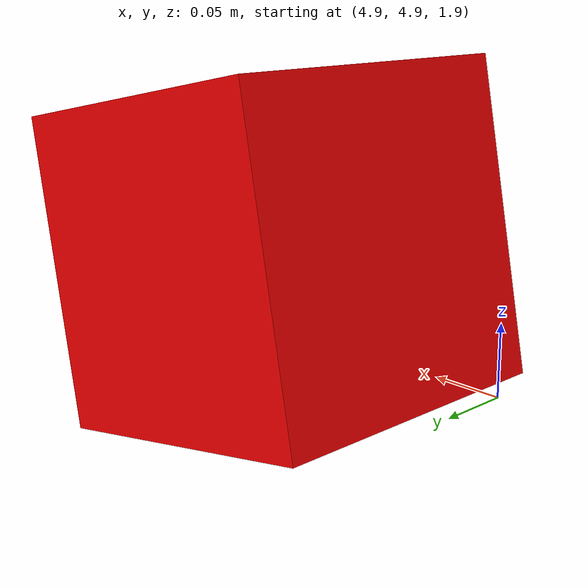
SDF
<?xml version="1.0" ?>
<sdf version="1.9">
  <world name="industrial_inspection_world">

    <physics name="1ms" type="dart">
      <max_step_size>0.001</max_step_size>
      <real_time_factor>1.0</real_time_factor>
    </physics>

    <plugin filename="ignition-gazebo-sensors-system" name="ignition::gazebo::systems::Sensors">
      <render_engine>ogre2</render_engine>
    </plugin>

    <light type="directional" name="sun">
      <cast_shadows>true</cast_shadows>
      <pose>0 0 10 0 0 0</pose>
      <diffuse>0.8 0.8 0.8 1</diffuse>
      <specular>0.2 0.2 0.2 1</specular>
      <direction>-0.5 0.1 -0.9</direction>
    </light>

    <model name="amr_inspection_facility">
      <include>
        <uri>model://amr_inspection_facility/model.sdf</uri>
        <pose>0 0 0 0 0 0</pose>
      </include>
    </model>

    <model name="thermal_camera_tester">
      <pose>5 5 2 0 0.2 0</pose>
      <static>false</static>
      <link name="link">
        <kinematic>true</kinematic> <gravity>false</gravity>

        <inertial>
          <mass>0.5</mass>
          <inertia>
            <ixx>0.001</ixx>
            <iyy>0.001</iyy>
            <izz>0.001</izz>
          </inertia>
        </inertial>

        <visual name="camera_visual">
          <geometry>
            <box>
              <size>0.2 0.2 0.2</size>
            </box>
          </geometry>
          <material>
            <ambient>1 0 0 1</ambient>
            <diffuse>1 0 0 1</diffuse>
          </material>
        </visual>

        <sensor name="thermal_camera" type="thermal">
          <camera>
            <horizontal_fov>1.047</horizontal_fov>
            <image>
              <width>640</width>
              <height>480</height>
              <format>R8G8B8</format>
            </image>
            <clip>
              <near>0.1</near>
              <far>100</far>
            </clip>
          </camera>
          <always_on>1</always_on>
          <update_rate>10</update_rate>
          <visualize>true</visualize>
          <topic>/thermal_camera/image</topic>
        </sensor>
      </link>
    </model>

    <plugin filename="gz-sim-scene-broadcaster-system" name="gz::sim::systems::SceneBroadcaster"/>
  </world>
</sdf>

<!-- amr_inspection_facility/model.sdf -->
<sdf version="1.6">
  <model name="amr_inspection_facility">

    <!-- مهم جداً تخليها true عشان المصنع ميبقاش طاير ويقع أو يتحرك لما الروبوت يخبط فيه -->
    <static>true</static>

    <link name="factory_base_link">

      <!-- 1. الجزء البصري (Visual) -->
      <!-- 2. جزء التصادم (Collision) -->
      <!-- انسخ الـ 5000 سطر بتوع مكعبات التصادم وحطهم هنا بالظبط -->

    <collision name="box_wall_1">
      <pose>0.0000 0.0000 0.0000 0.0000 -0.0000 0.0000</pose>
      <geometry>
        <box>
          <size>0.3000 0.2000 1.2000</size>
        </box>
      </geometry>
      <surface>
        <friction>
          <ode>
            <mu>0.5</mu>
            <mu2>0.5</mu2>
          </ode>
        </friction>
      </surface>
    </collision>

    <collision name="box_wall_2">
      <pose>0.0000 0.0000 0.0000 0.0000 -0.0000 0.0000</pose>
      <geometry>
        <box>
          <size>0.3000 0.2000 1.2000</size>
        </box>
      </geometry>
      <surface>
        <friction>
          <ode>
            <mu>0.5</mu>
            <mu2>0.5</mu2>
          </ode>
        </friction>
      </surface>
    </collision>

    <collision name="box_wall_3">
      <pose>0.0000 0.0000 0.0000 0.0000 -0.0000 0.0000</pose>
      <geometry>
        <box>
          <size>0.3000 0.2000 1.2000</size>
        </box>
      </geometry>
      <surface>
        <friction>
          <ode>
            <mu>0.5</mu>
            <mu2>0.5</mu2>
          </ode>
        </friction>
      </surface>
    </collision>

    <collision name="box_wall_4">
      <pose>0.0000 0.0000 0.0000 0.0000 -0.0000 0.0000</pose>
      <geometry>
        <box>
          <size>0.3000 0.0600 0.0400</size>
        </box>
      </geometry>
      <surface>
        <friction>
          <ode>
            <mu>0.5</mu>
            <mu2>0.5</mu2>
          </ode>
        </friction>
      </surface>
    </collision>

    <collision name="box_wall_5">
      <pose>0.0000 0.0000 0.0000 0.0000 -0.0000 0.0000</pose>
      <geometry>
        <box>
          <size>0.3000 0.0600 0.0400</size>
        </box>
      </geometry>
      <surface>
        <friction>
          <ode>
            <mu>0.5</mu>
            <mu2>0.5</mu2>
          </ode>
        </friction>
      </surface>
    </collision>

    <collision name="box_wall_6">
      <pose>0.0000 0.0000 0.0000 0.0000 -0.0000 0.0000</pose>
      <geometry>
        <box>
          <size>0.3000 0.2000 1.2000</size>
        </box>
      </geometry>
      <surface>
        <friction>
          <ode>
            <mu>0.5</mu>
            <mu2>0.5</mu2>
          </ode>
        </friction>
      </surface>
    </collision>

    <collision name="box_wall_7">
      <pose>0.0000 0.0000 0.0000 0.0000 -0.0000 0.0000</pose>
      <geometry>
        <box>
          <size>0.3000 0.0600 0.0400</size>
        </box>
      </geometry>
      <surface>
        <friction>
          <ode>
            <mu>0.5</mu>
            <mu2>0.5</mu2>
          </ode>
        </friction>
      </surface>
    </collision>

    <collision name="box_wall_8">
      <pose>0.0000 0.0000 0.0000 0.0000 -0.0000 0.0000</pose>
      <geometry>
        <box>
          <size>0.3000 0.0600 0.0400</size>
        </box>
      </geometry>
      <surface>
        <friction>
          <ode>
            <mu>0.5</mu>
            <mu2>0.5</mu2>
          </ode>
        </friction>
      </surface>
    </collision>

    <collision name="box_wall_9">
      <pose>0.0000 0.0000 0.0000 0.0000 -0.0000 0.0000</pose>
      <geometry>
        <box>
          <size>2.4000 0.8000 0.9500</size>
        </box>
      </geometry>
      <surface>
        <friction>
          <ode>
            <mu>0.5</mu>
            <mu2>0.5</mu2>
          </ode>
        </friction>
      </surface>
    </collision>

    <collision name="box_wall_10">
      <pose>0.0000 0.0000 0.0000 0.0000 -0.0000 0.0000</pose>
      <geometry>
        <box>
          <size>0.0600 0.0600 0.9000</size>
        </box>
      </geometry>
      <surface>
        <friction>
          <ode>
            <mu>0.5</mu>
            <mu2>0.5</mu2>
          </ode>
        </friction>
      </surface>
    </collision>

    <collision name="box_wall_11">
      <pose>0.0000 0.0000 0.0000 0.0000 -0.0000 0.0000</pose>
      <geometry>
        <box>
          <size>0.0600 0.0600 0.9000</size>
        </box>
      </geometry>
      <surface>
        <friction>
          <ode>
            <mu>0.5</mu>
            <mu2>0.5</mu2>
          </ode>
        </friction>
      </surface>
    </collision>

    <collision name="box_wall_12">
      <pose>0.0000 0.0000 0.0000 0.0000 -0.0000 0.0000</pose>
      <geometry>
        <box>
          <size>0.7000 0.5000 1.9000</size>
        </box>
      </geometry>
      <surface>
        <friction>
          <ode>
            <mu>0.5</mu>
            <mu2>0.5</mu2>
          </ode>
        </friction>
      </surface>
    </collision>

    <collision name="box_wall_13">
      <pose>0.0000 0.0000 0.0000 0.0000 -0.0000 0.0000</pose>
      <geometry>
        <box>
          <size>0.0200 0.4600 1.8600</size>
        </box>
      </geometry>
      <surface>
        <friction>
          <ode>
            <mu>0.5</mu>
            <mu2>0.5</mu2>
          </ode>
        </friction>
      </surface>
    </collision>

    <collision name="box_wall_14">
      <pose>0.0000 0.0000 0.0000 0.0000 -0.0000 0.0000</pose>
      <geometry>
        <box>
          <size>0.7000 0.5000 1.9000</size>
        </box>
      </geometry>
      <surface>
        <friction>
          <ode>
            <mu>0.5</mu>
            <mu2>0.5</mu2>
          </ode>
        </friction>
      </surface>
    </collision>

    <collision name="box_wall_15">
      <pose>0.0000 0.0000 0.0000 0.0000 -0.0000 0.0000</pose>
      <geometry>
        <box>
          <size>0.0200 0.4600 1.8600</size>
        </box>
      </geometry>
      <surface>
        <friction>
          <ode>
            <mu>0.5</mu>
            <mu2>0.5</mu2>
          </ode>
        </friction>
      </surface>
    </collision>

    <collision name="box_wall_16">
      <pose>0.0000 0.0000 0.0000 0.0000 -0.0000 0.0000</pose>
      <geometry>
        <box>
          <size>1.2000 0.9000 0.8000</size>
        </box>
      </geometry>
      <surface>
        <friction>
          <ode>
            <mu>0.5</mu>
            <mu2>0.5</mu2>
          </ode>
        </friction>
      </surface>
    </collision>

    <collision name="box_wall_17">
      <pose>0.0000 0.0000 0.0000 0.0000 -0.0000 0.0000</pose>
      <geometry>
        <box>
          <size>0.0600 0.0600 0.8000</size>
        </box>
      </geometry>
      <surface>
        <friction>
          <ode>
            <mu>0.5</mu>
            <mu2>0.5</mu2>
          </ode>
        </friction>
      </surface>
    </collision>

    <collision name="box_wall_18">
      <pose>0.0000 0.0000 0.0000 0.0000 -0.0000 0.0000</pose>
      <geometry>
        <box>
          <size>0.0600 0.0600 0.8000</size>
        </box>
      </geometry>
      <surface>
        <friction>
          <ode>
            <mu>0.5</mu>
            <mu2>0.5</mu2>
          </ode>
        </friction>
      </surface>
    </collision>

    <collision name="box_wall_19">
      <pose>0.0000 0.0000 0.0000 0.0000 -0.0000 0.0000</pose>
      <geometry>
        <box>
          <size>0.0600 0.0600 0.8000</size>
        </box>
      </geometry>
      <surface>
        <friction>
          <ode>
            <mu>0.5</mu>
            <mu2>0.5</mu2>
          </ode>
        </friction>
      </surface>
    </collision>

    <collision name="box_wall_20">
      <pose>0.0000 0.0000 0.0000 0.0000 -0.0000 0.0000</pose>
      <geometry>
        <box>
          <size>0.0600 0.0600 0.8000</size>
        </box>
      </geometry>
      <surface>
        <friction>
          <ode>
            <mu>0.5</mu>
            <mu2>0.5</mu2>
          </ode>
        </friction>
      </surface>
    </collision>

    <collision name="box_wall_21">
      <pose>0.0000 0.0000 0.0000 0.0000 -0.0000 0.0000</pose>
      <geometry>
        <box>
          <size>0.1600 0.0500 0.1600</size>
        </box>
      </geometry>
      <surface>
        <friction>
          <ode>
            <mu>0.5</mu>
            <mu2>0.5</mu2>
          </ode>
        </friction>
      </surface>
    </collision>

    <collision name="box_wall_22">
      <pose>0.0000 0.0000 0.0000 0.0000 -0.0000 0.0000</pose>
      <geometry>
        <box>
          <size>0.1400 0.1400 0.0050</size>
        </box>
      </geometry>
      <surface>
        <friction>
          <ode>
            <mu>0.5</mu>
            <mu2>0.5</mu2>
          </ode>
        </friction>
      </surface>
    </collision>

    <collision name="box_wall_23">
      <pose>0.0000 0.0000 0.0000 0.0000 -0.0000 0.0000</pose>
      <geometry>
        <box>
          <size>0.1500 0.0075 0.1500</size>
        </box>
      </geometry>
      <surface>
        <friction>
          <ode>
            <mu>0.5</mu>
            <mu2>0.5</mu2>
          </ode>
        </friction>
      </surface>
    </collision>

    <collision name="box_wall_24">
      <pose>0.0000 0.0000 0.0000 0.0000 -0.0000 0.0000</pose>
      <geometry>
        <box>
          <size>2.4100 2.4100 0.6000</size>
        </box>
      </geometry>
      <surface>
        <friction>
          <ode>
            <mu>0.5</mu>
            <mu2>0.5</mu2>
          </ode>
        </friction>
      </surface>
    </collision>

    <collision name="box_wall_25">
      <pose>0.0000 0.0000 0.0000 0.0000 -0.0000 0.0000</pose>
      <geometry>
        <box>
          <size>23.5000 0.2500 6.0000</size>
        </box>
      </geometry>
      <surface>
        <friction>
          <ode>
            <mu>0.5</mu>
            <mu2>0.5</mu2>
          </ode>
        </friction>
      </surface>
    </collision>

    <collision name="box_wall_26">
      <pose>0.0000 0.0000 0.0000 0.0000 -0.0000 0.0000</pose>
      <geometry>
        <box>
          <size>3.0000 0.2500 3.2000</size>
        </box>
      </geometry>
      <surface>
        <friction>
          <ode>
            <mu>0.5</mu>
            <mu2>0.5</mu2>
          </ode>
        </friction>
      </surface>
    </collision>

    <collision name="box_wall_27">
      <pose>0.0000 0.0000 0.0000 0.0000 -0.0000 0.0000</pose>
      <geometry>
        <box>
          <size>33.5000 0.2500 6.0000</size>
        </box>
      </geometry>
      <surface>
        <friction>
          <ode>
            <mu>0.5</mu>
            <mu2>0.5</mu2>
          </ode>
        </friction>
      </surface>
    </collision>

    <collision name="box_wall_28">
      <pose>0.0000 0.0000 0.0000 0.0000 -0.0000 0.0000</pose>
      <geometry>
        <box>
          <size>60.0000 0.2500 6.0000</size>
        </box>
      </geometry>
      <surface>
        <friction>
          <ode>
            <mu>0.5</mu>
            <mu2>0.5</mu2>
          </ode>
        </friction>
      </surface>
    </collision>

    <collision name="box_wall_29">
      <pose>0.0000 0.0000 0.0000 0.0000 -0.0000 0.0000</pose>
      <geometry>
        <box>
          <size>0.2500 19.2500 6.0000</size>
        </box>
      </geometry>
      <surface>
        <friction>
          <ode>
            <mu>0.5</mu>
            <mu2>0.5</mu2>
          </ode>
        </friction>
      </surface>
    </collision>

    <collision name="box_wall_30">
      <pose>0.0000 0.0000 0.0000 0.0000 -0.0000 0.0000</pose>
      <geometry>
        <box>
          <size>0.2500 3.0000 3.2000</size>
        </box>
      </geometry>
      <surface>
        <friction>
          <ode>
            <mu>0.5</mu>
            <mu2>0.5</mu2>
          </ode>
        </friction>
      </surface>
    </collision>

    <collision name="box_wall_31">
      <pose>0.0000 0.0000 0.0000 0.0000 -0.0000 0.0000</pose>
      <geometry>
        <box>
          <size>0.2500 17.7500 6.0000</size>
        </box>
      </geometry>
      <surface>
        <friction>
          <ode>
            <mu>0.5</mu>
            <mu2>0.5</mu2>
          </ode>
        </friction>
      </surface>
    </collision>

    <collision name="box_wall_32">
      <pose>0.0000 0.0000 0.0000 0.0000 -0.0000 0.0000</pose>
      <geometry>
        <box>
          <size>0.2500 19.2500 6.0000</size>
        </box>
      </geometry>
      <surface>
        <friction>
          <ode>
            <mu>0.5</mu>
            <mu2>0.5</mu2>
          </ode>
        </friction>
      </surface>
    </collision>

    <collision name="box_wall_33">
      <pose>0.0000 0.0000 0.0000 0.0000 -0.0000 0.0000</pose>
      <geometry>
        <box>
          <size>0.2500 3.0000 3.2000</size>
        </box>
      </geometry>
      <surface>
        <friction>
          <ode>
            <mu>0.5</mu>
            <mu2>0.5</mu2>
          </ode>
        </friction>
      </surface>
    </collision>

    <collision name="box_wall_34">
      <pose>0.0000 0.0000 0.0000 0.0000 -0.0000 0.0000</pose>
      <geometry>
        <box>
          <size>0.2500 17.7500 6.0000</size>
        </box>
      </geometry>
      <surface>
        <friction>
          <ode>
            <mu>0.5</mu>
            <mu2>0.5</mu2>
          </ode>
        </friction>
      </surface>
    </collision>

    <collision name="box_wall_35">
      <pose>0.0000 0.0000 0.0000 0.0000 -0.0000 0.0000</pose>
      <geometry>
        <box>
          <size>6.2500 0.2000 6.0000</size>
        </box>
      </geometry>
      <surface>
        <friction>
          <ode>
            <mu>0.5</mu>
            <mu2>0.5</mu2>
          </ode>
        </friction>
      </surface>
    </collision>

    <collision name="box_wall_36">
      <pose>0.0000 0.0000 0.0000 0.0000 -0.0000 0.0000</pose>
      <geometry>
        <box>
          <size>14.0000 0.2000 6.0000</size>
        </box>
      </geometry>
      <surface>
        <friction>
          <ode>
            <mu>0.5</mu>
            <mu2>0.5</mu2>
          </ode>
        </friction>
      </surface>
    </collision>

    <collision name="box_wall_37">
      <pose>0.0000 0.0000 0.0000 0.0000 -0.0000 0.0000</pose>
      <geometry>
        <box>
          <size>23.0000 0.2000 6.0000</size>
        </box>
      </geometry>
      <surface>
        <friction>
          <ode>
            <mu>0.5</mu>
            <mu2>0.5</mu2>
          </ode>
        </friction>
      </surface>
    </collision>

    <collision name="box_wall_38">
      <pose>0.0000 0.0000 0.0000 0.0000 -0.0000 0.0000</pose>
      <geometry>
        <box>
          <size>8.5000 0.2000 6.0000</size>
        </box>
      </geometry>
      <surface>
        <friction>
          <ode>
            <mu>0.5</mu>
            <mu2>0.5</mu2>
          </ode>
        </friction>
      </surface>
    </collision>

    <collision name="box_wall_39">
      <pose>0.0000 0.0000 0.0000 0.0000 -0.0000 0.0000</pose>
      <geometry>
        <box>
          <size>15.5000 0.2000 6.0000</size>
        </box>
      </geometry>
      <surface>
        <friction>
          <ode>
            <mu>0.5</mu>
            <mu2>0.5</mu2>
          </ode>
        </friction>
      </surface>
    </collision>

    <collision name="box_wall_40">
      <pose>0.0000 0.0000 0.0000 0.0000 -0.0000 0.0000</pose>
      <geometry>
        <box>
          <size>10.0500 0.2000 6.0000</size>
        </box>
      </geometry>
      <surface>
        <friction>
          <ode>
            <mu>0.5</mu>
            <mu2>0.5</mu2>
          </ode>
        </friction>
      </surface>
    </collision>

    <collision name="box_wall_41">
      <pose>0.0000 0.0000 0.0000 0.0000 -0.0000 0.0000</pose>
      <geometry>
        <box>
          <size>2.5000 0.2000 3.2000</size>
        </box>
      </geometry>
      <surface>
        <friction>
          <ode>
            <mu>0.5</mu>
            <mu2>0.5</mu2>
          </ode>
        </friction>
      </surface>
    </collision>

    <collision name="box_wall_42">
      <pose>0.0000 0.0000 0.0000 0.0000 -0.0000 0.0000</pose>
      <geometry>
        <box>
          <size>2.5000 0.2000 3.2000</size>
        </box>
      </geometry>
      <surface>
        <friction>
          <ode>
            <mu>0.5</mu>
            <mu2>0.5</mu2>
          </ode>
        </friction>
      </surface>
    </collision>

    <collision name="box_wall_43">
      <pose>0.0000 0.0000 0.0000 0.0000 -0.0000 0.0000</pose>
      <geometry>
        <box>
          <size>0.2000 5.8000 6.0000</size>
        </box>
      </geometry>
      <surface>
        <friction>
          <ode>
            <mu>0.5</mu>
            <mu2>0.5</mu2>
          </ode>
        </friction>
      </surface>
    </collision>

    <collision name="box_wall_44">
      <pose>0.0000 0.0000 0.0000 0.0000 -0.0000 0.0000</pose>
      <geometry>
        <box>
          <size>0.2000 2.0000 3.2000</size>
        </box>
      </geometry>
      <surface>
        <friction>
          <ode>
            <mu>0.5</mu>
            <mu2>0.5</mu2>
          </ode>
        </friction>
      </surface>
    </collision>

    <collision name="box_wall_45">
      <pose>0.0000 0.0000 0.0000 0.0000 -0.0000 0.0000</pose>
      <geometry>
        <box>
          <size>0.2000 9.0000 6.0000</size>
        </box>
      </geometry>
      <surface>
        <friction>
          <ode>
            <mu>0.5</mu>
            <mu2>0.5</mu2>
          </ode>
        </friction>
      </surface>
    </collision>

    <collision name="box_wall_46">
      <pose>0.0000 0.0000 0.0000 0.0000 -0.0000 0.0000</pose>
      <geometry>
        <box>
          <size>0.2000 5.8000 6.0000</size>
        </box>
      </geometry>
      <surface>
        <friction>
          <ode>
            <mu>0.5</mu>
            <mu2>0.5</mu2>
          </ode>
        </friction>
      </surface>
    </collision>

    <collision name="box_wall_47">
      <pose>0.0000 0.0000 0.0000 0.0000 -0.0000 0.0000</pose>
      <geometry>
        <box>
          <size>0.2000 1.8000 3.2000</size>
        </box>
      </geometry>
      <surface>
        <friction>
          <ode>
            <mu>0.5</mu>
            <mu2>0.5</mu2>
          </ode>
        </friction>
      </surface>
    </collision>

    <collision name="box_wall_48">
      <pose>0.0000 0.0000 0.0000 0.0000 -0.0000 0.0000</pose>
      <geometry>
        <box>
          <size>0.2000 9.2000 6.0000</size>
        </box>
      </geometry>
      <surface>
        <friction>
          <ode>
            <mu>0.5</mu>
            <mu2>0.5</mu2>
          </ode>
        </friction>
      </surface>
    </collision>

    <collision name="box_wall_49">
      <pose>0.0000 0.0000 0.0000 0.0000 -0.0000 0.0000</pose>
      <geometry>
        <box>
          <size>4.2500 0.2000 6.0000</size>
        </box>
      </geometry>
      <surface>
        <friction>
          <ode>
            <mu>0.5</mu>
            <mu2>0.5</mu2>
          </ode>
        </friction>
      </surface>
    </collision>

    <collision name="box_wall_50">
      <pose>0.0000 0.0000 0.0000 0.0000 -0.0000 0.0000</pose>
      <geometry>
        <box>
          <size>2.0000 0.2000 3.2000</size>
        </box>
      </geometry>
      <surface>
        <friction>
          <ode>
            <mu>0.5</mu>
            <mu2>0.5</mu2>
          </ode>
        </friction>
      </surface>
    </collision>

    <collision name="box_wall_51">
      <pose>0.0000 0.0000 0.0000 0.0000 -0.0000 0.0000</pose>
      <geometry>
        <box>
          <size>3.7500 0.2000 6.0000</size>
        </box>
      </geometry>
      <surface>
        <friction>
          <ode>
            <mu>0.5</mu>
            <mu2>0.5</mu2>
          </ode>
        </friction>
      </surface>
    </collision>

    <collision name="box_wall_52">
      <pose>0.0000 0.0000 0.0000 0.0000 -0.0000 0.0000</pose>
      <geometry>
        <box>
          <size>4.2500 0.2000 6.0000</size>
        </box>
      </geometry>
      <surface>
        <friction>
          <ode>
            <mu>0.5</mu>
            <mu2>0.5</mu2>
          </ode>
        </friction>
      </surface>
    </collision>

    <collision name="box_wall_53">
      <pose>0.0000 0.0000 0.0000 0.0000 -0.0000 0.0000</pose>
      <geometry>
        <box>
          <size>2.0000 0.2000 3.2000</size>
        </box>
      </geometry>
      <surface>
        <friction>
          <ode>
            <mu>0.5</mu>
            <mu2>0.5</mu2>
          </ode>
        </friction>
      </surface>
    </collision>

    <collision name="box_wall_54">
      <pose>0.0000 0.0000 0.0000 0.0000 -0.0000 0.0000</pose>
      <geometry>
        <box>
          <size>4.0000 0.2000 6.0000</size>
        </box>
      </geometry>
      <surface>
        <friction>
          <ode>
            <mu>0.5</mu>
            <mu2>0.5</mu2>
          </ode>
        </friction>
      </surface>
    </collision>

    <collision name="box_wall_55">
      <pose>0.0000 0.0000 0.0000 0.0000 -0.0000 0.0000</pose>
      <geometry>
        <box>
          <size>0.2000 19.2500 6.0000</size>
        </box>
      </geometry>
      <surface>
        <friction>
          <ode>
            <mu>0.5</mu>
            <mu2>0.5</mu2>
          </ode>
        </friction>
      </surface>
    </collision>

    <collision name="box_wall_56">
      <pose>0.0000 0.0000 0.0000 0.0000 -0.0000 0.0000</pose>
      <geometry>
        <box>
          <size>0.2000 19.2500 6.0000</size>
        </box>
      </geometry>
      <surface>
        <friction>
          <ode>
            <mu>0.5</mu>
            <mu2>0.5</mu2>
          </ode>
        </friction>
      </surface>
    </collision>

    <collision name="box_wall_57">
      <pose>0.0000 0.0000 0.0000 0.0000 -0.0000 0.0000</pose>
      <geometry>
        <box>
          <size>0.2000 19.2500 6.0000</size>
        </box>
      </geometry>
      <surface>
        <friction>
          <ode>
            <mu>0.5</mu>
            <mu2>0.5</mu2>
          </ode>
        </friction>
      </surface>
    </collision>

    <collision name="box_wall_58">
      <pose>0.0000 0.0000 0.0000 0.0000 -0.0000 0.0000</pose>
      <geometry>
        <box>
          <size>6.7500 0.2000 6.0000</size>
        </box>
      </geometry>
      <surface>
        <friction>
          <ode>
            <mu>0.5</mu>
            <mu2>0.5</mu2>
          </ode>
        </friction>
      </surface>
    </collision>

    <collision name="box_wall_59">
      <pose>0.0000 0.0000 0.0000 0.0000 -0.0000 0.0000</pose>
      <geometry>
        <box>
          <size>2.6600 0.1200 0.0800</size>
        </box>
      </geometry>
      <surface>
        <friction>
          <ode>
            <mu>0.5</mu>
            <mu2>0.5</mu2>
          </ode>
        </friction>
      </surface>
    </collision>

    <collision name="box_wall_60">
      <pose>0.0000 0.0000 0.0000 0.0000 -0.0000 0.0000</pose>
      <geometry>
        <box>
          <size>0.0800 0.1200 2.8000</size>
        </box>
      </geometry>
      <surface>
        <friction>
          <ode>
            <mu>0.5</mu>
            <mu2>0.5</mu2>
          </ode>
        </friction>
      </surface>
    </collision>

    <collision name="box_wall_61">
      <pose>0.0000 0.0000 0.0000 0.0000 -0.0000 0.0000</pose>
      <geometry>
        <box>
          <size>0.0800 0.1200 2.8000</size>
        </box>
      </geometry>
      <surface>
        <friction>
          <ode>
            <mu>0.5</mu>
            <mu2>0.5</mu2>
          </ode>
        </friction>
      </surface>
    </collision>

    <collision name="box_wall_62">
      <pose>0.0000 0.0000 0.0000 0.0000 -0.0000 0.0000</pose>
      <geometry>
        <box>
          <size>2.6600 0.1200 0.0800</size>
        </box>
      </geometry>
      <surface>
        <friction>
          <ode>
            <mu>0.5</mu>
            <mu2>0.5</mu2>
          </ode>
        </friction>
      </surface>
    </collision>

    <collision name="box_wall_63">
      <pose>0.0000 0.0000 0.0000 0.0000 -0.0000 0.0000</pose>
      <geometry>
        <box>
          <size>0.0800 0.1200 2.8000</size>
        </box>
      </geometry>
      <surface>
        <friction>
          <ode>
            <mu>0.5</mu>
            <mu2>0.5</mu2>
          </ode>
        </friction>
      </surface>
    </collision>

    <collision name="box_wall_64">
      <pose>0.0000 0.0000 0.0000 0.0000 -0.0000 0.0000</pose>
      <geometry>
        <box>
          <size>0.0800 0.1200 2.8000</size>
        </box>
      </geometry>
      <surface>
        <friction>
          <ode>
            <mu>0.5</mu>
            <mu2>0.5</mu2>
          </ode>
        </friction>
      </surface>
    </collision>

    <collision name="box_wall_65">
      <pose>0.0000 0.0000 0.0000 0.0000 -0.0000 0.0000</pose>
      <geometry>
        <box>
          <size>0.1200 2.1600 0.0800</size>
        </box>
      </geometry>
      <surface>
        <friction>
          <ode>
            <mu>0.5</mu>
            <mu2>0.5</mu2>
          </ode>
        </friction>
      </surface>
    </collision>

    <collision name="box_wall_66">
      <pose>0.0000 0.0000 0.0000 0.0000 -0.0000 0.0000</pose>
      <geometry>
        <box>
          <size>0.1200 0.0800 2.8000</size>
        </box>
      </geometry>
      <surface>
        <friction>
          <ode>
            <mu>0.5</mu>
            <mu2>0.5</mu2>
          </ode>
        </friction>
      </surface>
    </collision>

    <collision name="box_wall_67">
      <pose>0.0000 0.0000 0.0000 0.0000 -0.0000 0.0000</pose>
      <geometry>
        <box>
          <size>0.1200 0.0800 2.8000</size>
        </box>
      </geometry>
      <surface>
        <friction>
          <ode>
            <mu>0.5</mu>
            <mu2>0.5</mu2>
          </ode>
        </friction>
      </surface>
    </collision>

    <collision name="box_wall_68">
      <pose>0.0000 0.0000 0.0000 0.0000 -0.0000 0.0000</pose>
      <geometry>
        <box>
          <size>2.1600 0.1200 0.0800</size>
        </box>
      </geometry>
      <surface>
        <friction>
          <ode>
            <mu>0.5</mu>
            <mu2>0.5</mu2>
          </ode>
        </friction>
      </surface>
    </collision>

    <collision name="box_wall_69">
      <pose>0.0000 0.0000 0.0000 0.0000 -0.0000 0.0000</pose>
      <geometry>
        <box>
          <size>0.0800 0.1200 2.8000</size>
        </box>
      </geometry>
      <surface>
        <friction>
          <ode>
            <mu>0.5</mu>
            <mu2>0.5</mu2>
          </ode>
        </friction>
      </surface>
    </collision>

    <collision name="box_wall_70">
      <pose>0.0000 0.0000 0.0000 0.0000 -0.0000 0.0000</pose>
      <geometry>
        <box>
          <size>0.0800 0.1200 2.8000</size>
        </box>
      </geometry>
      <surface>
        <friction>
          <ode>
            <mu>0.5</mu>
            <mu2>0.5</mu2>
          </ode>
        </friction>
      </surface>
    </collision>

    <collision name="box_wall_71">
      <pose>0.0000 0.0000 0.0000 0.0000 -0.0000 0.0000</pose>
      <geometry>
        <box>
          <size>0.1200 1.9600 0.0800</size>
        </box>
      </geometry>
      <surface>
        <friction>
          <ode>
            <mu>0.5</mu>
            <mu2>0.5</mu2>
          </ode>
        </friction>
      </surface>
    </collision>

    <collision name="box_wall_72">
      <pose>0.0000 0.0000 0.0000 0.0000 -0.0000 0.0000</pose>
      <geometry>
        <box>
          <size>0.1200 0.0800 2.8000</size>
        </box>
      </geometry>
      <surface>
        <friction>
          <ode>
            <mu>0.5</mu>
            <mu2>0.5</mu2>
          </ode>
        </friction>
      </surface>
    </collision>

    <collision name="box_wall_73">
      <pose>0.0000 0.0000 0.0000 0.0000 -0.0000 0.0000</pose>
      <geometry>
        <box>
          <size>0.1200 0.0800 2.8000</size>
        </box>
      </geometry>
      <surface>
        <friction>
          <ode>
            <mu>0.5</mu>
            <mu2>0.5</mu2>
          </ode>
        </friction>
      </surface>
    </collision>

    <collision name="box_wall_74">
      <pose>0.0000 0.0000 0.0000 0.0000 -0.0000 0.0000</pose>
      <geometry>
        <box>
          <size>2.1600 0.1200 0.0800</size>
        </box>
      </geometry>
      <surface>
        <friction>
          <ode>
            <mu>0.5</mu>
            <mu2>0.5</mu2>
          </ode>
        </friction>
      </surface>
    </collision>

    <collision name="box_wall_75">
      <pose>0.0000 0.0000 0.0000 0.0000 -0.0000 0.0000</pose>
      <geometry>
        <box>
          <size>0.0800 0.1200 2.8000</size>
        </box>
      </geometry>
      <surface>
        <friction>
          <ode>
            <mu>0.5</mu>
            <mu2>0.5</mu2>
          </ode>
        </friction>
      </surface>
    </collision>

    <collision name="box_wall_76">
      <pose>0.0000 0.0000 0.0000 0.0000 -0.0000 0.0000</pose>
      <geometry>
        <box>
          <size>0.0800 0.1200 2.8000</size>
        </box>
      </geometry>
      <surface>
        <friction>
          <ode>
            <mu>0.5</mu>
            <mu2>0.5</mu2>
          </ode>
        </friction>
      </surface>
    </collision>

    <collision name="box_wall_77">
      <pose>0.0000 0.0000 0.0000 0.0000 -0.0000 0.0000</pose>
      <geometry>
        <box>
          <size>0.0800 0.1200 2.8000</size>
        </box>
      </geometry>
      <surface>
        <friction>
          <ode>
            <mu>0.5</mu>
            <mu2>0.5</mu2>
          </ode>
        </friction>
      </surface>
    </collision>

    <collision name="box_wall_78">
      <pose>0.0000 0.0000 0.0000 0.0000 -0.0000 0.0000</pose>
      <geometry>
        <box>
          <size>0.0800 0.1200 2.8000</size>
        </box>
      </geometry>
      <surface>
        <friction>
          <ode>
            <mu>0.5</mu>
            <mu2>0.5</mu2>
          </ode>
        </friction>
      </surface>
    </collision>

    <collision name="box_wall_79">
      <pose>0.0000 0.0000 0.0000 0.0000 -0.0000 0.0000</pose>
      <geometry>
        <box>
          <size>3.1600 0.1200 0.0800</size>
        </box>
      </geometry>
      <surface>
        <friction>
          <ode>
            <mu>0.5</mu>
            <mu2>0.5</mu2>
          </ode>
        </friction>
      </surface>
    </collision>

    <collision name="box_wall_80">
      <pose>0.0000 0.0000 0.0000 0.0000 -0.0000 0.0000</pose>
      <geometry>
        <box>
          <size>0.0800 0.1200 6.0000</size>
        </box>
      </geometry>
      <surface>
        <friction>
          <ode>
            <mu>0.5</mu>
            <mu2>0.5</mu2>
          </ode>
        </friction>
      </surface>
    </collision>

    <collision name="box_wall_81">
      <pose>0.0000 0.0000 0.0000 0.0000 -0.0000 0.0000</pose>
      <geometry>
        <box>
          <size>0.0800 0.1200 6.0000</size>
        </box>
      </geometry>
      <surface>
        <friction>
          <ode>
            <mu>0.5</mu>
            <mu2>0.5</mu2>
          </ode>
        </friction>
      </surface>
    </collision>

    <collision name="box_wall_82">
      <pose>0.0000 0.0000 0.0000 0.0000 -0.0000 0.0000</pose>
      <geometry>
        <box>
          <size>0.0800 0.1200 2.8000</size>
        </box>
      </geometry>
      <surface>
        <friction>
          <ode>
            <mu>0.5</mu>
            <mu2>0.5</mu2>
          </ode>
        </friction>
      </surface>
    </collision>

    <collision name="box_wall_83">
      <pose>0.0000 0.0000 0.0000 0.0000 -0.0000 0.0000</pose>
      <geometry>
        <box>
          <size>0.0800 0.1200 2.8000</size>
        </box>
      </geometry>
      <surface>
        <friction>
          <ode>
            <mu>0.5</mu>
            <mu2>0.5</mu2>
          </ode>
        </friction>
      </surface>
    </collision>

    <collision name="box_wall_84">
      <pose>0.0000 0.0000 0.0000 0.0000 -0.0000 0.0000</pose>
      <geometry>
        <box>
          <size>0.1200 3.1600 0.0800</size>
        </box>
      </geometry>
      <surface>
        <friction>
          <ode>
            <mu>0.5</mu>
            <mu2>0.5</mu2>
          </ode>
        </friction>
      </surface>
    </collision>

    <collision name="box_wall_85">
      <pose>0.0000 0.0000 0.0000 0.0000 -0.0000 0.0000</pose>
      <geometry>
        <box>
          <size>0.1200 0.0800 2.8000</size>
        </box>
      </geometry>
      <surface>
        <friction>
          <ode>
            <mu>0.5</mu>
            <mu2>0.5</mu2>
          </ode>
        </friction>
      </surface>
    </collision>

    <collision name="box_wall_86">
      <pose>0.0000 0.0000 0.0000 0.0000 -0.0000 0.0000</pose>
      <geometry>
        <box>
          <size>0.1200 0.0800 2.8000</size>
        </box>
      </geometry>
      <surface>
        <friction>
          <ode>
            <mu>0.5</mu>
            <mu2>0.5</mu2>
          </ode>
        </friction>
      </surface>
    </collision>

    <collision name="box_wall_87">
      <pose>0.0000 0.0000 0.0000 0.0000 -0.0000 0.0000</pose>
      <geometry>
        <box>
          <size>0.1200 3.1600 0.0800</size>
        </box>
      </geometry>
      <surface>
        <friction>
          <ode>
            <mu>0.5</mu>
            <mu2>0.5</mu2>
          </ode>
        </friction>
      </surface>
    </collision>

    <collision name="box_wall_88">
      <pose>0.0000 0.0000 0.0000 0.0000 -0.0000 0.0000</pose>
      <geometry>
        <box>
          <size>0.1200 0.0800 2.8000</size>
        </box>
      </geometry>
      <surface>
        <friction>
          <ode>
            <mu>0.5</mu>
            <mu2>0.5</mu2>
          </ode>
        </friction>
      </surface>
    </collision>

    <collision name="box_wall_89">
      <pose>0.0000 0.0000 0.0000 0.0000 -0.0000 0.0000</pose>
      <geometry>
        <box>
          <size>0.1200 0.0800 2.8000</size>
        </box>
      </geometry>
      <surface>
        <friction>
          <ode>
            <mu>0.5</mu>
            <mu2>0.5</mu2>
          </ode>
        </friction>
      </surface>
    </collision>

    <collision name="box_wall_90">
      <pose>0.0000 0.0000 0.0000 0.0000 -0.0000 0.0000</pose>
      <geometry>
        <box>
          <size>0.0500 2.9800 2.7800</size>
        </box>
      </geometry>
      <surface>
        <friction>
          <ode>
            <mu>0.5</mu>
            <mu2>0.5</mu2>
          </ode>
        </friction>
      </surface>
    </collision>

    <collision name="box_wall_91">
      <pose>0.0000 0.0000 0.0000 0.0000 -0.0000 0.0000</pose>
      <geometry>
        <box>
          <size>0.4000 0.4000 6.0000</size>
        </box>
      </geometry>
      <surface>
        <friction>
          <ode>
            <mu>0.5</mu>
            <mu2>0.5</mu2>
          </ode>
        </friction>
      </surface>
    </collision>

    <collision name="box_wall_92">
      <pose>0.0000 0.0000 0.0000 0.0000 -0.0000 0.0000</pose>
      <geometry>
        <box>
          <size>0.4000 0.4000 6.0000</size>
        </box>
      </geometry>
      <surface>
        <friction>
          <ode>
            <mu>0.5</mu>
            <mu2>0.5</mu2>
          </ode>
        </friction>
      </surface>
    </collision>

    <collision name="box_wall_93">
      <pose>0.0000 0.0000 0.0000 0.0000 -0.0000 0.0000</pose>
      <geometry>
        <box>
          <size>0.4000 0.4000 6.0000</size>
        </box>
      </geometry>
      <surface>
        <friction>
          <ode>
            <mu>0.5</mu>
            <mu2>0.5</mu2>
          </ode>
        </friction>
      </surface>
    </collision>

    <collision name="box_wall_94">
      <pose>0.0000 0.0000 0.0000 0.0000 -0.0000 0.0000</pose>
      <geometry>
        <box>
          <size>0.4000 0.4000 6.0000</size>
        </box>
      </geometry>
      <surface>
        <friction>
          <ode>
            <mu>0.5</mu>
            <mu2>0.5</mu2>
          </ode>
        </friction>
      </surface>
    </collision>

    <collision name="box_wall_95">
      <pose>0.0000 0.0000 0.0000 0.0000 -0.0000 0.0000</pose>
      <geometry>
        <box>
          <size>0.4000 0.4000 6.0000</size>
        </box>
      </geometry>
      <surface>
        <friction>
          <ode>
            <mu>0.5</mu>
            <mu2>0.5</mu2>
          </ode>
        </friction>
      </surface>
    </collision>

    <collision name="box_wall_96">
      <pose>0.0000 0.0000 0.0000 0.0000 -0.0000 0.0000</pose>
      <geometry>
        <box>
          <size>0.4000 0.4000 6.0000</size>
        </box>
      </geometry>
      <surface>
        <friction>
          <ode>
            <mu>0.5</mu>
            <mu2>0.5</mu2>
          </ode>
        </friction>
      </surface>
    </collision>

    <collision name="box_wall_97">
      <pose>0.0000 0.0000 0.0000 0.0000 -0.0000 0.0000</pose>
      <geometry>
        <box>
          <size>0.4000 0.4000 6.0000</size>
        </box>
      </geometry>
      <surface>
        <friction>
          <ode>
            <mu>0.5</mu>
            <mu2>0.5</mu2>
          </ode>
        </friction>
      </surface>
    </collision>

    <collision name="box_wall_98">
      <pose>0.0000 0.0000 0.0000 0.0000 -0.0000 0.0000</pose>
      <geometry>
        <box>
          <size>0.4000 0.4000 6.0000</size>
        </box>
      </geometry>
      <surface>
        <friction>
          <ode>
            <mu>0.5</mu>
            <mu2>0.5</mu2>
          </ode>
        </friction>
      </surface>
    </collision>

    <collision name="box_wall_99">
      <pose>0.0000 0.0000 0.0000 0.0000 -0.0000 0.0000</pose>
      <geometry>
        <box>
          <size>0.4000 0.4000 6.0000</size>
        </box>
      </geometry>
      <surface>
        <friction>
          <ode>
            <mu>0.5</mu>
            <mu2>0.5</mu2>
          </ode>
        </friction>
      </surface>
    </collision>

    <collision name="box_wall_100">
      <pose>0.0000 0.0000 0.0000 0.0000 -0.0000 0.0000</pose>
      <geometry>
        <box>
          <size>0.4000 0.4000 6.0000</size>
        </box>
      </geometry>
      <surface>
        <friction>
          <ode>
            <mu>0.5</mu>
            <mu2>0.5</mu2>
          </ode>
        </friction>
      </surface>
    </collision>

    <collision name="box_wall_101">
      <pose>0.0000 0.0000 0.0000 0.0000 -0.0000 0.0000</pose>
      <geometry>
        <box>
          <size>0.4000 0.4000 6.0000</size>
        </box>
      </geometry>
      <surface>
        <friction>
          <ode>
            <mu>0.5</mu>
            <mu2>0.5</mu2>
          </ode>
        </friction>
      </surface>
    </collision>

    <collision name="box_wall_102">
      <pose>0.0000 0.0000 0.0000 0.0000 -0.0000 0.0000</pose>
      <geometry>
        <box>
          <size>0.4000 0.4000 6.0000</size>
        </box>
      </geometry>
      <surface>
        <friction>
          <ode>
            <mu>0.5</mu>
            <mu2>0.5</mu2>
          </ode>
        </friction>
      </surface>
    </collision>

    <collision name="box_wall_103">
      <pose>0.0000 0.0000 0.0000 0.0000 -0.0000 0.0000</pose>
      <geometry>
        <box>
          <size>0.4000 0.4000 6.0000</size>
        </box>
      </geometry>
      <surface>
        <friction>
          <ode>
            <mu>0.5</mu>
            <mu2>0.5</mu2>
          </ode>
        </friction>
      </surface>
    </collision>

    <collision name="box_wall_104">
      <pose>0.0000 0.0000 0.0000 0.0000 -0.0000 0.0000</pose>
      <geometry>
        <box>
          <size>0.4000 0.4000 6.0000</size>
        </box>
      </geometry>
      <surface>
        <friction>
          <ode>
            <mu>0.5</mu>
            <mu2>0.5</mu2>
          </ode>
        </friction>
      </surface>
    </collision>

    <collision name="box_wall_105">
      <pose>0.0000 0.0000 0.0000 0.0000 -0.0000 0.0000</pose>
      <geometry>
        <box>
          <size>0.4000 0.4000 6.0000</size>
        </box>
      </geometry>
      <surface>
        <friction>
          <ode>
            <mu>0.5</mu>
            <mu2>0.5</mu2>
          </ode>
        </friction>
      </surface>
    </collision>

    <collision name="box_wall_106">
      <pose>0.0000 0.0000 0.0000 0.0000 -0.0000 0.0000</pose>
      <geometry>
        <box>
          <size>0.4000 0.4000 6.0000</size>
        </box>
      </geometry>
      <surface>
        <friction>
          <ode>
            <mu>0.5</mu>
            <mu2>0.5</mu2>
          </ode>
        </friction>
      </surface>
    </collision>

    <collision name="box_wall_107">
      <pose>0.0000 0.0000 0.0000 0.0000 -0.0000 0.0000</pose>
      <geometry>
        <box>
          <size>0.4000 0.4000 6.0000</size>
        </box>
      </geometry>
      <surface>
        <friction>
          <ode>
            <mu>0.5</mu>
            <mu2>0.5</mu2>
          </ode>
        </friction>
      </surface>
    </collision>

    <collision name="box_wall_108">
      <pose>0.0000 0.0000 0.0000 0.0000 -0.0000 0.0000</pose>
      <geometry>
        <box>
          <size>0.4000 0.4000 6.0000</size>
        </box>
      </geometry>
      <surface>
        <friction>
          <ode>
            <mu>0.5</mu>
            <mu2>0.5</mu2>
          </ode>
        </friction>
      </surface>
    </collision>

    <collision name="box_wall_109">
      <pose>0.0000 0.0000 0.0000 0.0000 -0.0000 0.0000</pose>
      <geometry>
        <box>
          <size>0.4000 0.4000 6.0000</size>
        </box>
      </geometry>
      <surface>
        <friction>
          <ode>
            <mu>0.5</mu>
            <mu2>0.5</mu2>
          </ode>
        </friction>
      </surface>
    </collision>

    <collision name="box_wall_110">
      <pose>0.0000 0.0000 0.0000 0.0000 -0.0000 0.0000</pose>
      <geometry>
        <box>
          <size>0.4000 0.4000 6.0000</size>
        </box>
      </geometry>
      <surface>
        <friction>
          <ode>
            <mu>0.5</mu>
            <mu2>0.5</mu2>
          </ode>
        </friction>
      </surface>
    </collision>

    <collision name="box_wall_111">
      <pose>0.0000 0.0000 0.0000 0.0000 -0.0000 0.0000</pose>
      <geometry>
        <box>
          <size>0.4000 0.4000 6.0000</size>
        </box>
      </geometry>
      <surface>
        <friction>
          <ode>
            <mu>0.5</mu>
            <mu2>0.5</mu2>
          </ode>
        </friction>
      </surface>
    </collision>

    <collision name="box_wall_112">
      <pose>0.0000 0.0000 0.0000 0.0000 -0.0000 0.0000</pose>
      <geometry>
        <box>
          <size>0.4000 0.4000 6.0000</size>
        </box>
      </geometry>
      <surface>
        <friction>
          <ode>
            <mu>0.5</mu>
            <mu2>0.5</mu2>
          </ode>
        </friction>
      </surface>
    </collision>

    <collision name="box_wall_113">
      <pose>0.0000 0.0000 0.0000 0.0000 -0.0000 0.0000</pose>
      <geometry>
        <box>
          <size>0.4000 0.4000 6.0000</size>
        </box>
      </geometry>
      <surface>
        <friction>
          <ode>
            <mu>0.5</mu>
            <mu2>0.5</mu2>
          </ode>
        </friction>
      </surface>
    </collision>

    <collision name="box_wall_114">
      <pose>0.0000 0.0000 0.0000 0.0000 -0.0000 0.0000</pose>
      <geometry>
        <box>
          <size>0.4000 0.4000 6.0000</size>
        </box>
      </geometry>
      <surface>
        <friction>
          <ode>
            <mu>0.5</mu>
            <mu2>0.5</mu2>
          </ode>
        </friction>
      </surface>
    </collision>

    <collision name="box_wall_115">
      <pose>0.0000 0.0000 0.0000 0.0000 -0.0000 0.0000</pose>
      <geometry>
        <box>
          <size>0.4000 0.4000 6.0000</size>
        </box>
      </geometry>
      <surface>
        <friction>
          <ode>
            <mu>0.5</mu>
            <mu2>0.5</mu2>
          </ode>
        </friction>
      </surface>
    </collision>

    <collision name="box_wall_116">
      <pose>0.0000 0.0000 0.0000 0.0000 -0.0000 0.0000</pose>
      <geometry>
        <box>
          <size>0.4000 0.4000 6.0000</size>
        </box>
      </geometry>
      <surface>
        <friction>
          <ode>
            <mu>0.5</mu>
            <mu2>0.5</mu2>
          </ode>
        </friction>
      </surface>
    </collision>

    <collision name="box_wall_117">
      <pose>0.0000 0.0000 0.0000 0.0000 -0.0000 0.0000</pose>
      <geometry>
        <box>
          <size>0.4000 0.4000 6.0000</size>
        </box>
      </geometry>
      <surface>
        <friction>
          <ode>
            <mu>0.5</mu>
            <mu2>0.5</mu2>
          </ode>
        </friction>
      </surface>
    </collision>

    <collision name="box_wall_118">
      <pose>0.0000 0.0000 0.0000 0.0000 -0.0000 0.0000</pose>
      <geometry>
        <box>
          <size>0.4000 0.4000 6.0000</size>
        </box>
      </geometry>
      <surface>
        <friction>
          <ode>
            <mu>0.5</mu>
            <mu2>0.5</mu2>
          </ode>
        </friction>
      </surface>
    </collision>

    <collision name="box_wall_119">
      <pose>0.0000 0.0000 0.0000 0.0000 -0.0000 0.0000</pose>
      <geometry>
        <box>
          <size>0.4000 0.4000 6.0000</size>
        </box>
      </geometry>
      <surface>
        <friction>
          <ode>
            <mu>0.5</mu>
            <mu2>0.5</mu2>
          </ode>
        </friction>
      </surface>
    </collision>

    <collision name="box_wall_120">
      <pose>0.0000 0.0000 0.0000 0.0000 -0.0000 0.0000</pose>
      <geometry>
        <box>
          <size>0.4000 0.4000 6.0000</size>
        </box>
      </geometry>
      <surface>
        <friction>
          <ode>
            <mu>0.5</mu>
            <mu2>0.5</mu2>
          </ode>
        </friction>
      </surface>
    </collision>

    <collision name="box_wall_121">
      <pose>0.0000 0.0000 0.0000 0.0000 -0.0000 0.0000</pose>
      <geometry>
        <box>
          <size>0.4000 0.4000 6.0000</size>
        </box>
      </geometry>
      <surface>
        <friction>
          <ode>
            <mu>0.5</mu>
            <mu2>0.5</mu2>
          </ode>
        </friction>
      </surface>
    </collision>

    <collision name="box_wall_122">
      <pose>0.0000 0.0000 0.0000 0.0000 -0.0000 0.0000</pose>
      <geometry>
        <box>
          <size>0.2000 0.0200 0.2000</size>
        </box>
      </geometry>
      <surface>
        <friction>
          <ode>
            <mu>0.5</mu>
            <mu2>0.5</mu2>
          </ode>
        </friction>
      </surface>
    </collision>

    <collision name="box_wall_123">
      <pose>0.0000 0.0000 0.0000 0.0000 -0.0000 0.0000</pose>
      <geometry>
        <box>
          <size>1.5000 0.9000 0.7000</size>
        </box>
      </geometry>
      <surface>
        <friction>
          <ode>
            <mu>0.5</mu>
            <mu2>0.5</mu2>
          </ode>
        </friction>
      </surface>
    </collision>

    <collision name="box_wall_124">
      <pose>0.0000 0.0000 0.0000 0.0000 -0.0000 0.0000</pose>
      <geometry>
        <box>
          <size>0.1600 0.1600 1.1000</size>
        </box>
      </geometry>
      <surface>
        <friction>
          <ode>
            <mu>0.5</mu>
            <mu2>0.5</mu2>
          </ode>
        </friction>
      </surface>
    </collision>

    <collision name="box_wall_125">
      <pose>0.0000 0.0000 0.0000 0.0000 -0.0000 0.0000</pose>
      <geometry>
        <box>
          <size>0.1500 0.1500 3.6000</size>
        </box>
      </geometry>
      <surface>
        <friction>
          <ode>
            <mu>0.5</mu>
            <mu2>0.5</mu2>
          </ode>
        </friction>
      </surface>
    </collision>

    <collision name="box_wall_126">
      <pose>0.0000 0.0000 0.0000 0.0000 -0.0000 0.0000</pose>
      <geometry>
        <box>
          <size>0.1200 1.8000 0.1200</size>
        </box>
      </geometry>
      <surface>
        <friction>
          <ode>
            <mu>0.5</mu>
            <mu2>0.5</mu2>
          </ode>
        </friction>
      </surface>
    </collision>

    <collision name="box_wall_127">
      <pose>0.0000 0.0000 0.0000 0.0000 -0.0000 0.0000</pose>
      <geometry>
        <box>
          <size>0.1200 1.5000 0.1200</size>
        </box>
      </geometry>
      <surface>
        <friction>
          <ode>
            <mu>0.5</mu>
            <mu2>0.5</mu2>
          </ode>
        </friction>
      </surface>
    </collision>

    <collision name="box_wall_128">
      <pose>0.0000 0.0000 0.0000 0.0000 -0.0000 0.0000</pose>
      <geometry>
        <box>
          <size>0.1500 0.1500 3.6000</size>
        </box>
      </geometry>
      <surface>
        <friction>
          <ode>
            <mu>0.5</mu>
            <mu2>0.5</mu2>
          </ode>
        </friction>
      </surface>
    </collision>

    <collision name="box_wall_129">
      <pose>0.0000 0.0000 0.0000 0.0000 -0.0000 0.0000</pose>
      <geometry>
        <box>
          <size>0.1200 1.8000 0.1200</size>
        </box>
      </geometry>
      <surface>
        <friction>
          <ode>
            <mu>0.5</mu>
            <mu2>0.5</mu2>
          </ode>
        </friction>
      </surface>
    </collision>

    <collision name="box_wall_130">
      <pose>0.0000 0.0000 0.0000 0.0000 -0.0000 0.0000</pose>
      <geometry>
        <box>
          <size>0.1200 1.5000 0.1200</size>
        </box>
      </geometry>
      <surface>
        <friction>
          <ode>
            <mu>0.5</mu>
            <mu2>0.5</mu2>
          </ode>
        </friction>
      </surface>
    </collision>

    <collision name="box_wall_131">
      <pose>0.0000 0.0000 0.0000 0.0000 -0.0000 0.0000</pose>
      <geometry>
        <box>
          <size>0.1200 1.5000 0.1200</size>
        </box>
      </geometry>
      <surface>
        <friction>
          <ode>
            <mu>0.5</mu>
            <mu2>0.5</mu2>
          </ode>
        </friction>
      </surface>
    </collision>

    <collision name="box_wall_132">
      <pose>0.0000 0.0000 0.0000 0.0000 -0.0000 0.0000</pose>
      <geometry>
        <box>
          <size>0.1500 0.1500 3.6000</size>
        </box>
      </geometry>
      <surface>
        <friction>
          <ode>
            <mu>0.5</mu>
            <mu2>0.5</mu2>
          </ode>
        </friction>
      </surface>
    </collision>

    <collision name="box_wall_133">
      <pose>0.0000 0.0000 0.0000 0.0000 -0.0000 0.0000</pose>
      <geometry>
        <box>
          <size>0.1200 1.8000 0.1200</size>
        </box>
      </geometry>
      <surface>
        <friction>
          <ode>
            <mu>0.5</mu>
            <mu2>0.5</mu2>
          </ode>
        </friction>
      </surface>
    </collision>

    <collision name="box_wall_134">
      <pose>0.0000 0.0000 0.0000 0.0000 -0.0000 0.0000</pose>
      <geometry>
        <box>
          <size>0.1200 1.5000 0.1200</size>
        </box>
      </geometry>
      <surface>
        <friction>
          <ode>
            <mu>0.5</mu>
            <mu2>0.5</mu2>
          </ode>
        </friction>
      </surface>
    </collision>

    <collision name="box_wall_135">
      <pose>0.0000 0.0000 0.0000 0.0000 -0.0000 0.0000</pose>
      <geometry>
        <box>
          <size>0.1500 0.1500 3.6000</size>
        </box>
      </geometry>
      <surface>
        <friction>
          <ode>
            <mu>0.5</mu>
            <mu2>0.5</mu2>
          </ode>
        </friction>
      </surface>
    </collision>

    <collision name="box_wall_136">
      <pose>0.0000 0.0000 0.0000 0.0000 -0.0000 0.0000</pose>
      <geometry>
        <box>
          <size>0.1200 1.8000 0.1200</size>
        </box>
      </geometry>
      <surface>
        <friction>
          <ode>
            <mu>0.5</mu>
            <mu2>0.5</mu2>
          </ode>
        </friction>
      </surface>
    </collision>

    <collision name="box_wall_137">
      <pose>0.0000 0.0000 0.0000 0.0000 -0.0000 0.0000</pose>
      <geometry>
        <box>
          <size>0.1200 1.5000 0.1200</size>
        </box>
      </geometry>
      <surface>
        <friction>
          <ode>
            <mu>0.5</mu>
            <mu2>0.5</mu2>
          </ode>
        </friction>
      </surface>
    </collision>

    <collision name="box_wall_138">
      <pose>0.0000 0.0000 0.0000 0.0000 -0.0000 0.0000</pose>
      <geometry>
        <box>
          <size>0.1500 0.1500 3.6000</size>
        </box>
      </geometry>
      <surface>
        <friction>
          <ode>
            <mu>0.5</mu>
            <mu2>0.5</mu2>
          </ode>
        </friction>
      </surface>
    </collision>

    <collision name="box_wall_139">
      <pose>0.0000 0.0000 0.0000 0.0000 -0.0000 0.0000</pose>
      <geometry>
        <box>
          <size>0.1200 1.8000 0.1200</size>
        </box>
      </geometry>
      <surface>
        <friction>
          <ode>
            <mu>0.5</mu>
            <mu2>0.5</mu2>
          </ode>
        </friction>
      </surface>
    </collision>

    <collision name="box_wall_140">
      <pose>0.0000 0.0000 0.0000 0.0000 -0.0000 0.0000</pose>
      <geometry>
        <box>
          <size>0.1200 1.5000 0.1200</size>
        </box>
      </geometry>
      <surface>
        <friction>
          <ode>
            <mu>0.5</mu>
            <mu2>0.5</mu2>
          </ode>
        </friction>
      </surface>
    </collision>

    <collision name="box_wall_141">
      <pose>0.0000 0.0000 0.0000 0.0000 -0.0000 0.0000</pose>
      <geometry>
        <box>
          <size>0.1500 0.1500 3.6000</size>
        </box>
      </geometry>
      <surface>
        <friction>
          <ode>
            <mu>0.5</mu>
            <mu2>0.5</mu2>
          </ode>
        </friction>
      </surface>
    </collision>

    <collision name="box_wall_142">
      <pose>0.0000 0.0000 0.0000 0.0000 -0.0000 0.0000</pose>
      <geometry>
        <box>
          <size>0.1200 1.8000 0.1200</size>
        </box>
      </geometry>
      <surface>
        <friction>
          <ode>
            <mu>0.5</mu>
            <mu2>0.5</mu2>
          </ode>
        </friction>
      </surface>
    </collision>

    <collision name="box_wall_143">
      <pose>0.0000 0.0000 0.0000 0.0000 -0.0000 0.0000</pose>
      <geometry>
        <box>
          <size>0.1200 1.5000 0.1200</size>
        </box>
      </geometry>
      <surface>
        <friction>
          <ode>
            <mu>0.5</mu>
            <mu2>0.5</mu2>
          </ode>
        </friction>
      </surface>
    </collision>

    <collision name="box_wall_144">
      <pose>0.0000 0.0000 0.0000 0.0000 -0.0000 0.0000</pose>
      <geometry>
        <box>
          <size>0.1500 0.1500 3.6000</size>
        </box>
      </geometry>
      <surface>
        <friction>
          <ode>
            <mu>0.5</mu>
            <mu2>0.5</mu2>
          </ode>
        </friction>
      </surface>
    </collision>

    <collision name="box_wall_145">
      <pose>0.0000 0.0000 0.0000 0.0000 -0.0000 0.0000</pose>
      <geometry>
        <box>
          <size>0.1200 1.8000 0.1200</size>
        </box>
      </geometry>
      <surface>
        <friction>
          <ode>
            <mu>0.5</mu>
            <mu2>0.5</mu2>
          </ode>
        </friction>
      </surface>
    </collision>

    <collision name="box_wall_146">
      <pose>0.0000 0.0000 0.0000 0.0000 -0.0000 0.0000</pose>
      <geometry>
        <box>
          <size>0.1200 1.5000 0.1200</size>
        </box>
      </geometry>
      <surface>
        <friction>
          <ode>
            <mu>0.5</mu>
            <mu2>0.5</mu2>
          </ode>
        </friction>
      </surface>
    </collision>

    <collision name="box_wall_147">
      <pose>0.0000 0.0000 0.0000 0.0000 -0.0000 0.0000</pose>
      <geometry>
        <box>
          <size>0.1500 0.1500 3.6000</size>
        </box>
      </geometry>
      <surface>
        <friction>
          <ode>
            <mu>0.5</mu>
            <mu2>0.5</mu2>
          </ode>
        </friction>
      </surface>
    </collision>

    <collision name="box_wall_148">
      <pose>0.0000 0.0000 0.0000 0.0000 -0.0000 0.0000</pose>
      <geometry>
        <box>
          <size>0.1200 1.8000 0.1200</size>
        </box>
      </geometry>
      <surface>
        <friction>
          <ode>
            <mu>0.5</mu>
            <mu2>0.5</mu2>
          </ode>
        </friction>
      </surface>
    </collision>

    <collision name="box_wall_149">
      <pose>0.0000 0.0000 0.0000 0.0000 -0.0000 0.0000</pose>
      <geometry>
        <box>
          <size>0.1200 1.5000 0.1200</size>
        </box>
      </geometry>
      <surface>
        <friction>
          <ode>
            <mu>0.5</mu>
            <mu2>0.5</mu2>
          </ode>
        </friction>
      </surface>
    </collision>

    <collision name="box_wall_150">
      <pose>0.0000 0.0000 0.0000 0.0000 -0.0000 0.0000</pose>
      <geometry>
        <box>
          <size>0.1600 0.5400 0.1600</size>
        </box>
      </geometry>
      <surface>
        <friction>
          <ode>
            <mu>0.5</mu>
            <mu2>0.5</mu2>
          </ode>
        </friction>
      </surface>
    </collision>

    <collision name="box_wall_151">
      <pose>0.0000 0.0000 0.0000 0.0000 -0.0000 0.0000</pose>
      <geometry>
        <box>
          <size>0.1600 0.1600 0.5200</size>
        </box>
      </geometry>
      <surface>
        <friction>
          <ode>
            <mu>0.5</mu>
            <mu2>0.5</mu2>
          </ode>
        </friction>
      </surface>
    </collision>

    <collision name="box_wall_152">
      <pose>0.0000 0.0000 0.0000 0.0000 -0.0000 0.0000</pose>
      <geometry>
        <box>
          <size>0.1600 0.5400 0.1600</size>
        </box>
      </geometry>
      <surface>
        <friction>
          <ode>
            <mu>0.5</mu>
            <mu2>0.5</mu2>
          </ode>
        </friction>
      </surface>
    </collision>

    <collision name="box_wall_153">
      <pose>0.0000 0.0000 0.0000 0.0000 -0.0000 0.0000</pose>
      <geometry>
        <box>
          <size>0.1600 0.1600 0.5200</size>
        </box>
      </geometry>
      <surface>
        <friction>
          <ode>
            <mu>0.5</mu>
            <mu2>0.5</mu2>
          </ode>
        </friction>
      </surface>
    </collision>

    <collision name="box_wall_154">
      <pose>0.0000 0.0000 0.0000 0.0000 -0.0000 0.0000</pose>
      <geometry>
        <box>
          <size>0.1600 0.5400 0.1600</size>
        </box>
      </geometry>
      <surface>
        <friction>
          <ode>
            <mu>0.5</mu>
            <mu2>0.5</mu2>
          </ode>
        </friction>
      </surface>
    </collision>

    <collision name="box_wall_155">
      <pose>0.0000 0.0000 0.0000 0.0000 -0.0000 0.0000</pose>
      <geometry>
        <box>
          <size>35.0000 0.2400 0.2400</size>
        </box>
      </geometry>
      <surface>
        <friction>
          <ode>
            <mu>0.5</mu>
            <mu2>0.5</mu2>
          </ode>
        </friction>
      </surface>
    </collision>

    <collision name="box_wall_156">
      <pose>0.0000 0.0000 0.0000 0.0000 -0.0000 0.0000</pose>
      <geometry>
        <box>
          <size>35.0000 0.1600 0.1600</size>
        </box>
      </geometry>
      <surface>
        <friction>
          <ode>
            <mu>0.5</mu>
            <mu2>0.5</mu2>
          </ode>
        </friction>
      </surface>
    </collision>

    <collision name="box_wall_157">
      <pose>0.0000 0.0000 0.0000 0.0000 -0.0000 0.0000</pose>
      <geometry>
        <box>
          <size>11.0000 0.2000 0.2000</size>
        </box>
      </geometry>
      <surface>
        <friction>
          <ode>
            <mu>0.5</mu>
            <mu2>0.5</mu2>
          </ode>
        </friction>
      </surface>
    </collision>

    <collision name="box_wall_158">
      <pose>0.0000 0.0000 0.0000 0.0000 -0.0000 0.0000</pose>
      <geometry>
        <box>
          <size>11.0000 0.1600 0.1600</size>
        </box>
      </geometry>
      <surface>
        <friction>
          <ode>
            <mu>0.5</mu>
            <mu2>0.5</mu2>
          </ode>
        </friction>
      </surface>
    </collision>

    <collision name="box_wall_159">
      <pose>0.0000 0.0000 0.0000 0.0000 -0.0000 0.0000</pose>
      <geometry>
        <box>
          <size>11.0000 0.1600 0.1600</size>
        </box>
      </geometry>
      <surface>
        <friction>
          <ode>
            <mu>0.5</mu>
            <mu2>0.5</mu2>
          </ode>
        </friction>
      </surface>
    </collision>

    <collision name="box_wall_160">
      <pose>0.0000 0.0000 0.0000 0.0000 -0.0000 0.0000</pose>
      <geometry>
        <box>
          <size>0.2000 10.3090 0.2000</size>
        </box>
      </geometry>
      <surface>
        <friction>
          <ode>
            <mu>0.5</mu>
            <mu2>0.5</mu2>
          </ode>
        </friction>
      </surface>
    </collision>

    <collision name="box_wall_161">
      <pose>0.0000 0.0000 0.0000 0.0000 -0.0000 0.0000</pose>
      <geometry>
        <box>
          <size>0.2000 0.5000 0.2000</size>
        </box>
      </geometry>
      <surface>
        <friction>
          <ode>
            <mu>0.5</mu>
            <mu2>0.5</mu2>
          </ode>
        </friction>
      </surface>
    </collision>

    <collision name="box_wall_162">
      <pose>0.0000 0.0000 0.0000 0.0000 -0.0000 0.0000</pose>
      <geometry>
        <box>
          <size>0.2000 10.3090 0.2000</size>
        </box>
      </geometry>
      <surface>
        <friction>
          <ode>
            <mu>0.5</mu>
            <mu2>0.5</mu2>
          </ode>
        </friction>
      </surface>
    </collision>

    <collision name="box_wall_163">
      <pose>0.0000 0.0000 0.0000 0.0000 -0.0000 0.0000</pose>
      <geometry>
        <box>
          <size>0.2000 0.5000 0.2000</size>
        </box>
      </geometry>
      <surface>
        <friction>
          <ode>
            <mu>0.5</mu>
            <mu2>0.5</mu2>
          </ode>
        </friction>
      </surface>
    </collision>

    <collision name="box_wall_164">
      <pose>0.0000 0.0000 0.0000 0.0000 -0.0000 0.0000</pose>
      <geometry>
        <box>
          <size>0.2000 0.5000 0.2000</size>
        </box>
      </geometry>
      <surface>
        <friction>
          <ode>
            <mu>0.5</mu>
            <mu2>0.5</mu2>
          </ode>
        </friction>
      </surface>
    </collision>

    <collision name="box_wall_165">
      <pose>0.0000 0.0000 0.0000 0.0000 -0.0000 0.0000</pose>
      <geometry>
        <box>
          <size>0.2000 0.5000 0.2000</size>
        </box>
      </geometry>
      <surface>
        <friction>
          <ode>
            <mu>0.5</mu>
            <mu2>0.5</mu2>
          </ode>
        </friction>
      </surface>
    </collision>

    <collision name="box_wall_166">
      <pose>0.0000 0.0000 0.0000 0.0000 -0.0000 0.0000</pose>
      <geometry>
        <box>
          <size>0.2800 0.2400 0.2800</size>
        </box>
      </geometry>
      <surface>
        <friction>
          <ode>
            <mu>0.5</mu>
            <mu2>0.5</mu2>
          </ode>
        </friction>
      </surface>
    </collision>

    <collision name="box_wall_167">
      <pose>0.0000 0.0000 0.0000 0.0000 -0.0000 0.0000</pose>
      <geometry>
        <box>
          <size>0.4000 0.4000 0.0300</size>
        </box>
      </geometry>
      <surface>
        <friction>
          <ode>
            <mu>0.5</mu>
            <mu2>0.5</mu2>
          </ode>
        </friction>
      </surface>
    </collision>

    <collision name="box_wall_168">
      <pose>0.0000 0.0000 0.0000 0.0000 -0.0000 0.0000</pose>
      <geometry>
        <box>
          <size>0.0500 0.0500 0.2400</size>
        </box>
      </geometry>
      <surface>
        <friction>
          <ode>
            <mu>0.5</mu>
            <mu2>0.5</mu2>
          </ode>
        </friction>
      </surface>
    </collision>

    <collision name="box_wall_169">
      <pose>0.0000 0.0000 0.0000 0.0000 -0.0000 0.0000</pose>
      <geometry>
        <box>
          <size>0.2800 0.2400 0.2800</size>
        </box>
      </geometry>
      <surface>
        <friction>
          <ode>
            <mu>0.5</mu>
            <mu2>0.5</mu2>
          </ode>
        </friction>
      </surface>
    </collision>

    <collision name="box_wall_170">
      <pose>0.0000 0.0000 0.0000 0.0000 -0.0000 0.0000</pose>
      <geometry>
        <box>
          <size>0.4000 0.4000 0.0300</size>
        </box>
      </geometry>
      <surface>
        <friction>
          <ode>
            <mu>0.5</mu>
            <mu2>0.5</mu2>
          </ode>
        </friction>
      </surface>
    </collision>

    <collision name="box_wall_171">
      <pose>0.0000 0.0000 0.0000 0.0000 -0.0000 0.0000</pose>
      <geometry>
        <box>
          <size>0.0500 0.0500 0.2400</size>
        </box>
      </geometry>
      <surface>
        <friction>
          <ode>
            <mu>0.5</mu>
            <mu2>0.5</mu2>
          </ode>
        </friction>
      </surface>
    </collision>

    <collision name="box_wall_172">
      <pose>0.0000 0.0000 0.0000 0.0000 -0.0000 0.0000</pose>
      <geometry>
        <box>
          <size>0.2800 0.2400 0.2800</size>
        </box>
      </geometry>
      <surface>
        <friction>
          <ode>
            <mu>0.5</mu>
            <mu2>0.5</mu2>
          </ode>
        </friction>
      </surface>
    </collision>

    <collision name="box_wall_173">
      <pose>0.0000 0.0000 0.0000 0.0000 -0.0000 0.0000</pose>
      <geometry>
        <box>
          <size>0.4000 0.4000 0.0300</size>
        </box>
      </geometry>
      <surface>
        <friction>
          <ode>
            <mu>0.5</mu>
            <mu2>0.5</mu2>
          </ode>
        </friction>
      </surface>
    </collision>

    <collision name="box_wall_174">
      <pose>0.0000 0.0000 0.0000 0.0000 -0.0000 0.0000</pose>
      <geometry>
        <box>
          <size>0.0500 0.0500 0.2400</size>
        </box>
      </geometry>
      <surface>
        <friction>
          <ode>
            <mu>0.5</mu>
            <mu2>0.5</mu2>
          </ode>
        </friction>
      </surface>
    </collision>

    <collision name="box_wall_175">
      <pose>0.0000 0.0000 0.0000 0.0000 -0.0000 0.0000</pose>
      <geometry>
        <box>
          <size>0.2800 0.2400 0.2800</size>
        </box>
      </geometry>
      <surface>
        <friction>
          <ode>
            <mu>0.5</mu>
            <mu2>0.5</mu2>
          </ode>
        </friction>
      </surface>
    </collision>

    <collision name="box_wall_176">
      <pose>0.0000 0.0000 0.0000 0.0000 -0.0000 0.0000</pose>
      <geometry>
        <box>
          <size>0.4000 0.4000 0.0300</size>
        </box>
      </geometry>
      <surface>
        <friction>
          <ode>
            <mu>0.5</mu>
            <mu2>0.5</mu2>
          </ode>
        </friction>
      </surface>
    </collision>

    <collision name="box_wall_177">
      <pose>0.0000 0.0000 0.0000 0.0000 -0.0000 0.0000</pose>
      <geometry>
        <box>
          <size>0.0500 0.0500 0.2400</size>
        </box>
      </geometry>
      <surface>
        <friction>
          <ode>
            <mu>0.5</mu>
            <mu2>0.5</mu2>
          </ode>
        </friction>
      </surface>
    </collision>

    <collision name="box_wall_178">
      <pose>0.0000 0.0000 0.0000 0.0000 -0.0000 0.0000</pose>
      <geometry>
        <box>
          <size>0.2800 0.2400 0.2800</size>
        </box>
      </geometry>
      <surface>
        <friction>
          <ode>
            <mu>0.5</mu>
            <mu2>0.5</mu2>
          </ode>
        </friction>
      </surface>
    </collision>

    <collision name="box_wall_179">
      <pose>0.0000 0.0000 0.0000 0.0000 -0.0000 0.0000</pose>
      <geometry>
        <box>
          <size>0.4000 0.4000 0.0300</size>
        </box>
      </geometry>
      <surface>
        <friction>
          <ode>
            <mu>0.5</mu>
            <mu2>0.5</mu2>
          </ode>
        </friction>
      </surface>
    </collision>

    <collision name="box_wall_180">
      <pose>0.0000 0.0000 0.0000 0.0000 -0.0000 0.0000</pose>
      <geometry>
        <box>
          <size>0.0500 0.0500 0.2400</size>
        </box>
      </geometry>
      <surface>
        <friction>
          <ode>
            <mu>0.5</mu>
            <mu2>0.5</mu2>
          </ode>
        </friction>
      </surface>
    </collision>

    <collision name="box_wall_181">
      <pose>0.0000 0.0000 0.0000 0.0000 -0.0000 0.0000</pose>
      <geometry>
        <box>
          <size>0.4000 0.4000 0.0600</size>
        </box>
      </geometry>
      <surface>
        <friction>
          <ode>
            <mu>0.5</mu>
            <mu2>0.5</mu2>
          </ode>
        </friction>
      </surface>
    </collision>

    <collision name="box_wall_182">
      <pose>0.0000 0.0000 0.0000 0.0000 -0.0000 0.0000</pose>
      <geometry>
        <box>
          <size>2.2000 1.1000 0.7700</size>
        </box>
      </geometry>
      <surface>
        <friction>
          <ode>
            <mu>0.5</mu>
            <mu2>0.5</mu2>
          </ode>
        </friction>
      </surface>
    </collision>

    <collision name="box_wall_183">
      <pose>0.0000 0.0000 0.0000 0.0000 -0.0000 0.0000</pose>
      <geometry>
        <box>
          <size>0.6000 0.8000 2.2900</size>
        </box>
      </geometry>
      <surface>
        <friction>
          <ode>
            <mu>0.5</mu>
            <mu2>0.5</mu2>
          </ode>
        </friction>
      </surface>
    </collision>

    <collision name="box_wall_184">
      <pose>0.0000 0.0000 0.0000 0.0000 -0.0000 0.0000</pose>
      <geometry>
        <box>
          <size>0.6000 0.8000 2.2900</size>
        </box>
      </geometry>
      <surface>
        <friction>
          <ode>
            <mu>0.5</mu>
            <mu2>0.5</mu2>
          </ode>
        </friction>
      </surface>
    </collision>

    <collision name="box_wall_185">
      <pose>0.0000 0.0000 0.0000 0.0000 -0.0000 0.0000</pose>
      <geometry>
        <box>
          <size>0.6000 0.8000 2.2900</size>
        </box>
      </geometry>
      <surface>
        <friction>
          <ode>
            <mu>0.5</mu>
            <mu2>0.5</mu2>
          </ode>
        </friction>
      </surface>
    </collision>

    <collision name="box_wall_186">
      <pose>0.0000 0.0000 0.0000 0.0000 -0.0000 0.0000</pose>
      <geometry>
        <box>
          <size>0.6000 0.8000 2.2900</size>
        </box>
      </geometry>
      <surface>
        <friction>
          <ode>
            <mu>0.5</mu>
            <mu2>0.5</mu2>
          </ode>
        </friction>
      </surface>
    </collision>

    <collision name="box_wall_187">
      <pose>0.0000 0.0000 0.0000 0.0000 -0.0000 0.0000</pose>
      <geometry>
        <box>
          <size>0.6000 0.8000 2.2900</size>
        </box>
      </geometry>
      <surface>
        <friction>
          <ode>
            <mu>0.5</mu>
            <mu2>0.5</mu2>
          </ode>
        </friction>
      </surface>
    </collision>

    <collision name="box_wall_188">
      <pose>0.0000 0.0000 0.0000 0.0000 -0.0000 0.0000</pose>
      <geometry>
        <box>
          <size>0.6000 0.8000 2.2900</size>
        </box>
      </geometry>
      <surface>
        <friction>
          <ode>
            <mu>0.5</mu>
            <mu2>0.5</mu2>
          </ode>
        </friction>
      </surface>
    </collision>

    <collision name="box_wall_189">
      <pose>0.0000 0.0000 0.0000 0.0000 -0.0000 0.0000</pose>
      <geometry>
        <box>
          <size>0.6000 0.8000 2.2900</size>
        </box>
      </geometry>
      <surface>
        <friction>
          <ode>
            <mu>0.5</mu>
            <mu2>0.5</mu2>
          </ode>
        </friction>
      </surface>
    </collision>

    <collision name="box_wall_190">
      <pose>0.0000 0.0000 0.0000 0.0000 -0.0000 0.0000</pose>
      <geometry>
        <box>
          <size>0.6000 0.8000 2.2900</size>
        </box>
      </geometry>
      <surface>
        <friction>
          <ode>
            <mu>0.5</mu>
            <mu2>0.5</mu2>
          </ode>
        </friction>
      </surface>
    </collision>

    <collision name="box_wall_191">
      <pose>0.0000 0.0000 0.0000 0.0000 -0.0000 0.0000</pose>
      <geometry>
        <box>
          <size>0.0400 0.0400 0.1800</size>
        </box>
      </geometry>
      <surface>
        <friction>
          <ode>
            <mu>0.5</mu>
            <mu2>0.5</mu2>
          </ode>
        </friction>
      </surface>
    </collision>

    <collision name="box_wall_192">
      <pose>0.0000 0.0000 0.0000 0.0000 -0.0000 0.0000</pose>
      <geometry>
        <box>
          <size>0.5000 0.7000 2.0000</size>
        </box>
      </geometry>
      <surface>
        <friction>
          <ode>
            <mu>0.5</mu>
            <mu2>0.5</mu2>
          </ode>
        </friction>
      </surface>
    </collision>

    <collision name="box_wall_193">
      <pose>0.0000 0.0000 0.0000 0.0000 -0.0000 0.0000</pose>
      <geometry>
        <box>
          <size>0.5000 0.7000 2.0000</size>
        </box>
      </geometry>
      <surface>
        <friction>
          <ode>
            <mu>0.5</mu>
            <mu2>0.5</mu2>
          </ode>
        </friction>
      </surface>
    </collision>

    <collision name="box_wall_194">
      <pose>0.0000 0.0000 0.0000 0.0000 -0.0000 0.0000</pose>
      <geometry>
        <box>
          <size>0.5000 0.7000 2.0000</size>
        </box>
      </geometry>
      <surface>
        <friction>
          <ode>
            <mu>0.5</mu>
            <mu2>0.5</mu2>
          </ode>
        </friction>
      </surface>
    </collision>

    <collision name="box_wall_195">
      <pose>0.0000 0.0000 0.0000 0.0000 -0.0000 0.0000</pose>
      <geometry>
        <box>
          <size>0.5000 0.7000 2.0000</size>
        </box>
      </geometry>
      <surface>
        <friction>
          <ode>
            <mu>0.5</mu>
            <mu2>0.5</mu2>
          </ode>
        </friction>
      </surface>
    </collision>

    <collision name="box_wall_196">
      <pose>0.0000 0.0000 0.0000 0.0000 -0.0000 0.0000</pose>
      <geometry>
        <box>
          <size>0.5000 0.7000 2.0000</size>
        </box>
      </geometry>
      <surface>
        <friction>
          <ode>
            <mu>0.5</mu>
            <mu2>0.5</mu2>
          </ode>
        </friction>
      </surface>
    </collision>

    <collision name="box_wall_197">
      <pose>0.0000 0.0000 0.0000 0.0000 -0.0000 0.0000</pose>
      <geometry>
        <box>
          <size>0.5000 0.7000 2.0000</size>
        </box>
      </geometry>
      <surface>
        <friction>
          <ode>
            <mu>0.5</mu>
            <mu2>0.5</mu2>
          </ode>
        </friction>
      </surface>
    </collision>

    <collision name="box_wall_198">
      <pose>0.0000 0.0000 0.0000 0.0000 -0.0000 0.0000</pose>
      <geometry>
        <box>
          <size>1.3000 1.1000 1.3000</size>
        </box>
      </geometry>
      <surface>
        <friction>
          <ode>
            <mu>0.5</mu>
            <mu2>0.5</mu2>
          </ode>
        </friction>
      </surface>
    </collision>

    <collision name="box_wall_199">
      <pose>0.0000 0.0000 0.0000 0.0000 -0.0000 0.0000</pose>
      <geometry>
        <box>
          <size>1.3000 1.1000 1.3000</size>
        </box>
      </geometry>
      <surface>
        <friction>
          <ode>
            <mu>0.5</mu>
            <mu2>0.5</mu2>
          </ode>
        </friction>
      </surface>
    </collision>

    <collision name="box_wall_200">
      <pose>0.0000 0.0000 0.0000 0.0000 -0.0000 0.0000</pose>
      <geometry>
        <box>
          <size>1.3000 1.1000 1.3000</size>
        </box>
      </geometry>
      <surface>
        <friction>
          <ode>
            <mu>0.5</mu>
            <mu2>0.5</mu2>
          </ode>
        </friction>
      </surface>
    </collision>

    <collision name="box_wall_201">
      <pose>0.0000 0.0000 0.0000 0.0000 -0.0000 0.0000</pose>
      <geometry>
        <box>
          <size>1.3000 1.1000 1.3000</size>
        </box>
      </geometry>
      <surface>
        <friction>
          <ode>
            <mu>0.5</mu>
            <mu2>0.5</mu2>
          </ode>
        </friction>
      </surface>
    </collision>

    <collision name="box_wall_202">
      <pose>0.0000 0.0000 0.0000 0.0000 -0.0000 0.0000</pose>
      <geometry>
        <box>
          <size>0.1000 0.1000 2.5000</size>
        </box>
      </geometry>
      <surface>
        <friction>
          <ode>
            <mu>0.5</mu>
            <mu2>0.5</mu2>
          </ode>
        </friction>
      </surface>
    </collision>

    <collision name="box_wall_203">
      <pose>0.0000 0.0000 0.0000 0.0000 -0.0000 0.0000</pose>
      <geometry>
        <box>
          <size>0.1000 0.1000 2.5000</size>
        </box>
      </geometry>
      <surface>
        <friction>
          <ode>
            <mu>0.5</mu>
            <mu2>0.5</mu2>
          </ode>
        </friction>
      </surface>
    </collision>

    <collision name="box_wall_204">
      <pose>0.0000 0.0000 0.0000 0.0000 -0.0000 0.0000</pose>
      <geometry>
        <box>
          <size>0.0600 0.0600 2.2361</size>
        </box>
      </geometry>
      <surface>
        <friction>
          <ode>
            <mu>0.5</mu>
            <mu2>0.5</mu2>
          </ode>
        </friction>
      </surface>
    </collision>

    <collision name="box_wall_205">
      <pose>0.0000 0.0000 0.0000 0.0000 -0.0000 0.0000</pose>
      <geometry>
        <box>
          <size>0.1000 0.1000 2.5000</size>
        </box>
      </geometry>
      <surface>
        <friction>
          <ode>
            <mu>0.5</mu>
            <mu2>0.5</mu2>
          </ode>
        </friction>
      </surface>
    </collision>

    <collision name="box_wall_206">
      <pose>0.0000 0.0000 0.0000 0.0000 -0.0000 0.0000</pose>
      <geometry>
        <box>
          <size>0.1000 0.1000 2.5000</size>
        </box>
      </geometry>
      <surface>
        <friction>
          <ode>
            <mu>0.5</mu>
            <mu2>0.5</mu2>
          </ode>
        </friction>
      </surface>
    </collision>

    <collision name="box_wall_207">
      <pose>0.0000 0.0000 0.0000 0.0000 -0.0000 0.0000</pose>
      <geometry>
        <box>
          <size>1.0000 2.6000 0.0800</size>
        </box>
      </geometry>
      <surface>
        <friction>
          <ode>
            <mu>0.5</mu>
            <mu2>0.5</mu2>
          </ode>
        </friction>
      </surface>
    </collision>

    <collision name="box_wall_208">
      <pose>0.0000 0.0000 0.0000 0.0000 -0.0000 0.0000</pose>
      <geometry>
        <box>
          <size>0.1000 0.1000 2.5000</size>
        </box>
      </geometry>
      <surface>
        <friction>
          <ode>
            <mu>0.5</mu>
            <mu2>0.5</mu2>
          </ode>
        </friction>
      </surface>
    </collision>

    <collision name="box_wall_209">
      <pose>0.0000 0.0000 0.0000 0.0000 -0.0000 0.0000</pose>
      <geometry>
        <box>
          <size>0.1000 0.1000 2.5000</size>
        </box>
      </geometry>
      <surface>
        <friction>
          <ode>
            <mu>0.5</mu>
            <mu2>0.5</mu2>
          </ode>
        </friction>
      </surface>
    </collision>

    <collision name="box_wall_210">
      <pose>0.0000 0.0000 0.0000 0.0000 -0.0000 0.0000</pose>
      <geometry>
        <box>
          <size>0.1000 0.1000 2.5000</size>
        </box>
      </geometry>
      <surface>
        <friction>
          <ode>
            <mu>0.5</mu>
            <mu2>0.5</mu2>
          </ode>
        </friction>
      </surface>
    </collision>

    <collision name="box_wall_211">
      <pose>0.0000 0.0000 0.0000 0.0000 -0.0000 0.0000</pose>
      <geometry>
        <box>
          <size>0.1000 0.1000 2.5000</size>
        </box>
      </geometry>
      <surface>
        <friction>
          <ode>
            <mu>0.5</mu>
            <mu2>0.5</mu2>
          </ode>
        </friction>
      </surface>
    </collision>

    <collision name="box_wall_212">
      <pose>0.0000 0.0000 0.0000 0.0000 -0.0000 0.0000</pose>
      <geometry>
        <box>
          <size>0.1000 0.1000 2.5000</size>
        </box>
      </geometry>
      <surface>
        <friction>
          <ode>
            <mu>0.5</mu>
            <mu2>0.5</mu2>
          </ode>
        </friction>
      </surface>
    </collision>

    <collision name="box_wall_213">
      <pose>0.0000 0.0000 0.0000 0.0000 -0.0000 0.0000</pose>
      <geometry>
        <box>
          <size>0.1000 0.1000 2.5000</size>
        </box>
      </geometry>
      <surface>
        <friction>
          <ode>
            <mu>0.5</mu>
            <mu2>0.5</mu2>
          </ode>
        </friction>
      </surface>
    </collision>

    <collision name="box_wall_214">
      <pose>0.0000 0.0000 0.0000 0.0000 -0.0000 0.0000</pose>
      <geometry>
        <box>
          <size>0.1000 0.1000 2.5000</size>
        </box>
      </geometry>
      <surface>
        <friction>
          <ode>
            <mu>0.5</mu>
            <mu2>0.5</mu2>
          </ode>
        </friction>
      </surface>
    </collision>

    <collision name="box_wall_215">
      <pose>0.0000 0.0000 0.0000 0.0000 -0.0000 0.0000</pose>
      <geometry>
        <box>
          <size>0.1000 0.1000 2.5000</size>
        </box>
      </geometry>
      <surface>
        <friction>
          <ode>
            <mu>0.5</mu>
            <mu2>0.5</mu2>
          </ode>
        </friction>
      </surface>
    </collision>

    <collision name="box_wall_216">
      <pose>0.0000 0.0000 0.0000 0.0000 -0.0000 0.0000</pose>
      <geometry>
        <box>
          <size>0.1000 0.1000 2.5000</size>
        </box>
      </geometry>
      <surface>
        <friction>
          <ode>
            <mu>0.5</mu>
            <mu2>0.5</mu2>
          </ode>
        </friction>
      </surface>
    </collision>

    <collision name="box_wall_217">
      <pose>0.0000 0.0000 0.0000 0.0000 -0.0000 0.0000</pose>
      <geometry>
        <box>
          <size>0.1000 0.1000 2.5000</size>
        </box>
      </geometry>
      <surface>
        <friction>
          <ode>
            <mu>0.5</mu>
            <mu2>0.5</mu2>
          </ode>
        </friction>
      </surface>
    </collision>

    <collision name="box_wall_218">
      <pose>0.0000 0.0000 0.0000 0.0000 -0.0000 0.0000</pose>
      <geometry>
        <box>
          <size>0.1000 0.1000 2.5000</size>
        </box>
      </geometry>
      <surface>
        <friction>
          <ode>
            <mu>0.5</mu>
            <mu2>0.5</mu2>
          </ode>
        </friction>
      </surface>
    </collision>

    <collision name="box_wall_219">
      <pose>0.0000 0.0000 0.0000 0.0000 -0.0000 0.0000</pose>
      <geometry>
        <box>
          <size>0.1000 0.1000 2.5000</size>
        </box>
      </geometry>
      <surface>
        <friction>
          <ode>
            <mu>0.5</mu>
            <mu2>0.5</mu2>
          </ode>
        </friction>
      </surface>
    </collision>

    <collision name="box_wall_220">
      <pose>0.0000 0.0000 0.0000 0.0000 -0.0000 0.0000</pose>
      <geometry>
        <box>
          <size>0.1000 0.1000 2.5000</size>
        </box>
      </geometry>
      <surface>
        <friction>
          <ode>
            <mu>0.5</mu>
            <mu2>0.5</mu2>
          </ode>
        </friction>
      </surface>
    </collision>

    <collision name="box_wall_221">
      <pose>0.0000 0.0000 0.0000 0.0000 -0.0000 0.0000</pose>
      <geometry>
        <box>
          <size>0.1000 0.1000 2.5000</size>
        </box>
      </geometry>
      <surface>
        <friction>
          <ode>
            <mu>0.5</mu>
            <mu2>0.5</mu2>
          </ode>
        </friction>
      </surface>
    </collision>

    <collision name="box_wall_222">
      <pose>0.0000 0.0000 0.0000 0.0000 -0.0000 0.0000</pose>
      <geometry>
        <box>
          <size>0.1000 0.1000 2.5000</size>
        </box>
      </geometry>
      <surface>
        <friction>
          <ode>
            <mu>0.5</mu>
            <mu2>0.5</mu2>
          </ode>
        </friction>
      </surface>
    </collision>

    <collision name="box_wall_223">
      <pose>0.0000 0.0000 0.0000 0.0000 -0.0000 0.0000</pose>
      <geometry>
        <box>
          <size>0.1000 0.1000 2.5000</size>
        </box>
      </geometry>
      <surface>
        <friction>
          <ode>
            <mu>0.5</mu>
            <mu2>0.5</mu2>
          </ode>
        </friction>
      </surface>
    </collision>

    <collision name="box_wall_224">
      <pose>0.0000 0.0000 0.0000 0.0000 -0.0000 0.0000</pose>
      <geometry>
        <box>
          <size>0.1000 0.1000 2.5000</size>
        </box>
      </geometry>
      <surface>
        <friction>
          <ode>
            <mu>0.5</mu>
            <mu2>0.5</mu2>
          </ode>
        </friction>
      </surface>
    </collision>

    <collision name="box_wall_225">
      <pose>0.0000 0.0000 0.0000 0.0000 -0.0000 0.0000</pose>
      <geometry>
        <box>
          <size>0.1000 0.1000 2.5000</size>
        </box>
      </geometry>
      <surface>
        <friction>
          <ode>
            <mu>0.5</mu>
            <mu2>0.5</mu2>
          </ode>
        </friction>
      </surface>
    </collision>

    <collision name="box_wall_226">
      <pose>0.0000 0.0000 0.0000 0.0000 -0.0000 0.0000</pose>
      <geometry>
        <box>
          <size>0.0600 0.0600 2.2361</size>
        </box>
      </geometry>
      <surface>
        <friction>
          <ode>
            <mu>0.5</mu>
            <mu2>0.5</mu2>
          </ode>
        </friction>
      </surface>
    </collision>

    <collision name="box_wall_227">
      <pose>0.0000 0.0000 0.0000 0.0000 -0.0000 0.0000</pose>
      <geometry>
        <box>
          <size>0.1000 0.1000 2.5000</size>
        </box>
      </geometry>
      <surface>
        <friction>
          <ode>
            <mu>0.5</mu>
            <mu2>0.5</mu2>
          </ode>
        </friction>
      </surface>
    </collision>

    <collision name="box_wall_228">
      <pose>0.0000 0.0000 0.0000 0.0000 -0.0000 0.0000</pose>
      <geometry>
        <box>
          <size>0.1000 0.1000 2.5000</size>
        </box>
      </geometry>
      <surface>
        <friction>
          <ode>
            <mu>0.5</mu>
            <mu2>0.5</mu2>
          </ode>
        </friction>
      </surface>
    </collision>

    <collision name="box_wall_229">
      <pose>0.0000 0.0000 0.0000 0.0000 -0.0000 0.0000</pose>
      <geometry>
        <box>
          <size>0.1000 0.1000 2.5000</size>
        </box>
      </geometry>
      <surface>
        <friction>
          <ode>
            <mu>0.5</mu>
            <mu2>0.5</mu2>
          </ode>
        </friction>
      </surface>
    </collision>

    <collision name="box_wall_230">
      <pose>0.0000 0.0000 0.0000 0.0000 -0.0000 0.0000</pose>
      <geometry>
        <box>
          <size>0.1000 0.1000 2.5000</size>
        </box>
      </geometry>
      <surface>
        <friction>
          <ode>
            <mu>0.5</mu>
            <mu2>0.5</mu2>
          </ode>
        </friction>
      </surface>
    </collision>

    <collision name="box_wall_231">
      <pose>0.0000 0.0000 0.0000 0.0000 -0.0000 0.0000</pose>
      <geometry>
        <box>
          <size>0.1000 0.1000 2.5000</size>
        </box>
      </geometry>
      <surface>
        <friction>
          <ode>
            <mu>0.5</mu>
            <mu2>0.5</mu2>
          </ode>
        </friction>
      </surface>
    </collision>

    <collision name="box_wall_232">
      <pose>0.0000 0.0000 0.0000 0.0000 -0.0000 0.0000</pose>
      <geometry>
        <box>
          <size>0.1000 0.1000 2.5000</size>
        </box>
      </geometry>
      <surface>
        <friction>
          <ode>
            <mu>0.5</mu>
            <mu2>0.5</mu2>
          </ode>
        </friction>
      </surface>
    </collision>

    <collision name="box_wall_233">
      <pose>0.0000 0.0000 0.0000 0.0000 -0.0000 0.0000</pose>
      <geometry>
        <box>
          <size>0.1000 0.1000 2.5000</size>
        </box>
      </geometry>
      <surface>
        <friction>
          <ode>
            <mu>0.5</mu>
            <mu2>0.5</mu2>
          </ode>
        </friction>
      </surface>
    </collision>

    <collision name="box_wall_234">
      <pose>0.0000 0.0000 0.0000 0.0000 -0.0000 0.0000</pose>
      <geometry>
        <box>
          <size>0.1000 0.1000 2.5000</size>
        </box>
      </geometry>
      <surface>
        <friction>
          <ode>
            <mu>0.5</mu>
            <mu2>0.5</mu2>
          </ode>
        </friction>
      </surface>
    </collision>

    <collision name="box_wall_235">
      <pose>0.0000 0.0000 0.0000 0.0000 -0.0000 0.0000</pose>
      <geometry>
        <box>
          <size>0.1000 0.1000 2.5000</size>
        </box>
      </geometry>
      <surface>
        <friction>
          <ode>
            <mu>0.5</mu>
            <mu2>0.5</mu2>
          </ode>
        </friction>
      </surface>
    </collision>

    <collision name="box_wall_236">
      <pose>0.0000 0.0000 0.0000 0.0000 -0.0000 0.0000</pose>
      <geometry>
        <box>
          <size>0.1000 0.1000 2.5000</size>
        </box>
      </geometry>
      <surface>
        <friction>
          <ode>
            <mu>0.5</mu>
            <mu2>0.5</mu2>
          </ode>
        </friction>
      </surface>
    </collision>

    <collision name="box_wall_237">
      <pose>0.0000 0.0000 0.0000 0.0000 -0.0000 0.0000</pose>
      <geometry>
        <box>
          <size>1.0000 2.6000 0.0800</size>
        </box>
      </geometry>
      <surface>
        <friction>
          <ode>
            <mu>0.5</mu>
            <mu2>0.5</mu2>
          </ode>
        </friction>
      </surface>
    </collision>

    <collision name="box_wall_238">
      <pose>0.0000 0.0000 0.0000 0.0000 -0.0000 0.0000</pose>
      <geometry>
        <box>
          <size>0.1000 0.1000 2.5000</size>
        </box>
      </geometry>
      <surface>
        <friction>
          <ode>
            <mu>0.5</mu>
            <mu2>0.5</mu2>
          </ode>
        </friction>
      </surface>
    </collision>

    <collision name="box_wall_239">
      <pose>0.0000 0.0000 0.0000 0.0000 -0.0000 0.0000</pose>
      <geometry>
        <box>
          <size>0.1000 0.1000 2.5000</size>
        </box>
      </geometry>
      <surface>
        <friction>
          <ode>
            <mu>0.5</mu>
            <mu2>0.5</mu2>
          </ode>
        </friction>
      </surface>
    </collision>

    <collision name="box_wall_240">
      <pose>0.0000 0.0000 0.0000 0.0000 -0.0000 0.0000</pose>
      <geometry>
        <box>
          <size>0.1000 0.1000 2.5000</size>
        </box>
      </geometry>
      <surface>
        <friction>
          <ode>
            <mu>0.5</mu>
            <mu2>0.5</mu2>
          </ode>
        </friction>
      </surface>
    </collision>

    <collision name="box_wall_241">
      <pose>0.0000 0.0000 0.0000 0.0000 -0.0000 0.0000</pose>
      <geometry>
        <box>
          <size>0.1000 0.1000 2.5000</size>
        </box>
      </geometry>
      <surface>
        <friction>
          <ode>
            <mu>0.5</mu>
            <mu2>0.5</mu2>
          </ode>
        </friction>
      </surface>
    </collision>

    <collision name="box_wall_242">
      <pose>0.0000 0.0000 0.0000 0.0000 -0.0000 0.0000</pose>
      <geometry>
        <box>
          <size>0.1000 0.1000 2.5000</size>
        </box>
      </geometry>
      <surface>
        <friction>
          <ode>
            <mu>0.5</mu>
            <mu2>0.5</mu2>
          </ode>
        </friction>
      </surface>
    </collision>

    <collision name="box_wall_243">
      <pose>0.0000 0.0000 0.0000 0.0000 -0.0000 0.0000</pose>
      <geometry>
        <box>
          <size>0.1000 0.1000 2.5000</size>
        </box>
      </geometry>
      <surface>
        <friction>
          <ode>
            <mu>0.5</mu>
            <mu2>0.5</mu2>
          </ode>
        </friction>
      </surface>
    </collision>

    <collision name="box_wall_244">
      <pose>0.0000 0.0000 0.0000 0.0000 -0.0000 0.0000</pose>
      <geometry>
        <box>
          <size>0.1000 0.1000 2.5000</size>
        </box>
      </geometry>
      <surface>
        <friction>
          <ode>
            <mu>0.5</mu>
            <mu2>0.5</mu2>
          </ode>
        </friction>
      </surface>
    </collision>

    <collision name="box_wall_245">
      <pose>0.0000 0.0000 0.0000 0.0000 -0.0000 0.0000</pose>
      <geometry>
        <box>
          <size>0.1000 0.1000 2.5000</size>
        </box>
      </geometry>
      <surface>
        <friction>
          <ode>
            <mu>0.5</mu>
            <mu2>0.5</mu2>
          </ode>
        </friction>
      </surface>
    </collision>

    <collision name="box_wall_246">
      <pose>0.0000 0.0000 0.0000 0.0000 -0.0000 0.0000</pose>
      <geometry>
        <box>
          <size>0.1000 0.1000 2.5000</size>
        </box>
      </geometry>
      <surface>
        <friction>
          <ode>
            <mu>0.5</mu>
            <mu2>0.5</mu2>
          </ode>
        </friction>
      </surface>
    </collision>

    <collision name="box_wall_247">
      <pose>0.0000 0.0000 0.0000 0.0000 -0.0000 0.0000</pose>
      <geometry>
        <box>
          <size>0.1000 0.1000 2.5000</size>
        </box>
      </geometry>
      <surface>
        <friction>
          <ode>
            <mu>0.5</mu>
            <mu2>0.5</mu2>
          </ode>
        </friction>
      </surface>
    </collision>

    <collision name="box_wall_248">
      <pose>0.0000 0.0000 0.0000 0.0000 -0.0000 0.0000</pose>
      <geometry>
        <box>
          <size>0.1000 0.1000 2.5000</size>
        </box>
      </geometry>
      <surface>
        <friction>
          <ode>
            <mu>0.5</mu>
            <mu2>0.5</mu2>
          </ode>
        </friction>
      </surface>
    </collision>

    <collision name="box_wall_249">
      <pose>0.0000 0.0000 0.0000 0.0000 -0.0000 0.0000</pose>
      <geometry>
        <box>
          <size>0.1000 0.1000 2.5000</size>
        </box>
      </geometry>
      <surface>
        <friction>
          <ode>
            <mu>0.5</mu>
            <mu2>0.5</mu2>
          </ode>
        </friction>
      </surface>
    </collision>

    <collision name="box_wall_250">
      <pose>0.0000 0.0000 0.0000 0.0000 -0.0000 0.0000</pose>
      <geometry>
        <box>
          <size>1.0000 2.6000 0.0800</size>
        </box>
      </geometry>
      <surface>
        <friction>
          <ode>
            <mu>0.5</mu>
            <mu2>0.5</mu2>
          </ode>
        </friction>
      </surface>
    </collision>

    <collision name="box_wall_251">
      <pose>0.0000 0.0000 0.0000 0.0000 -0.0000 0.0000</pose>
      <geometry>
        <box>
          <size>1.0000 2.6000 0.0800</size>
        </box>
      </geometry>
      <surface>
        <friction>
          <ode>
            <mu>0.5</mu>
            <mu2>0.5</mu2>
          </ode>
        </friction>
      </surface>
    </collision>

    <collision name="box_wall_252">
      <pose>0.0000 0.0000 0.0000 0.0000 -0.0000 0.0000</pose>
      <geometry>
        <box>
          <size>1.0000 2.6000 0.0800</size>
        </box>
      </geometry>
      <surface>
        <friction>
          <ode>
            <mu>0.5</mu>
            <mu2>0.5</mu2>
          </ode>
        </friction>
      </surface>
    </collision>

    <collision name="box_wall_253">
      <pose>0.0000 0.0000 0.0000 0.0000 -0.0000 0.0000</pose>
      <geometry>
        <box>
          <size>0.1000 0.1000 2.5000</size>
        </box>
      </geometry>
      <surface>
        <friction>
          <ode>
            <mu>0.5</mu>
            <mu2>0.5</mu2>
          </ode>
        </friction>
      </surface>
    </collision>

    <collision name="box_wall_254">
      <pose>0.0000 0.0000 0.0000 0.0000 -0.0000 0.0000</pose>
      <geometry>
        <box>
          <size>0.1000 0.1000 2.5000</size>
        </box>
      </geometry>
      <surface>
        <friction>
          <ode>
            <mu>0.5</mu>
            <mu2>0.5</mu2>
          </ode>
        </friction>
      </surface>
    </collision>

    <collision name="box_wall_255">
      <pose>0.0000 0.0000 0.0000 0.0000 -0.0000 0.0000</pose>
      <geometry>
        <box>
          <size>0.1000 0.1000 2.5000</size>
        </box>
      </geometry>
      <surface>
        <friction>
          <ode>
            <mu>0.5</mu>
            <mu2>0.5</mu2>
          </ode>
        </friction>
      </surface>
    </collision>

    <collision name="box_wall_256">
      <pose>0.0000 0.0000 0.0000 0.0000 -0.0000 0.0000</pose>
      <geometry>
        <box>
          <size>0.1000 0.1000 2.5000</size>
        </box>
      </geometry>
      <surface>
        <friction>
          <ode>
            <mu>0.5</mu>
            <mu2>0.5</mu2>
          </ode>
        </friction>
      </surface>
    </collision>

    <collision name="box_wall_257">
      <pose>0.0000 0.0000 0.0000 0.0000 -0.0000 0.0000</pose>
      <geometry>
        <box>
          <size>1.0000 2.6000 0.0800</size>
        </box>
      </geometry>
      <surface>
        <friction>
          <ode>
            <mu>0.5</mu>
            <mu2>0.5</mu2>
          </ode>
        </friction>
      </surface>
    </collision>

    <collision name="box_wall_258">
      <pose>0.0000 0.0000 0.0000 0.0000 -0.0000 0.0000</pose>
      <geometry>
        <box>
          <size>1.0000 2.6000 0.0800</size>
        </box>
      </geometry>
      <surface>
        <friction>
          <ode>
            <mu>0.5</mu>
            <mu2>0.5</mu2>
          </ode>
        </friction>
      </surface>
    </collision>

    <collision name="box_wall_259">
      <pose>0.0000 0.0000 0.0000 0.0000 -0.0000 0.0000</pose>
      <geometry>
        <box>
          <size>1.0000 2.6000 0.0800</size>
        </box>
      </geometry>
      <surface>
        <friction>
          <ode>
            <mu>0.5</mu>
            <mu2>0.5</mu2>
          </ode>
        </friction>
      </surface>
    </collision>

    <collision name="box_wall_260">
      <pose>0.0000 0.0000 0.0000 0.0000 -0.0000 0.0000</pose>
      <geometry>
        <box>
          <size>0.1000 0.1000 2.5000</size>
        </box>
      </geometry>
      <surface>
        <friction>
          <ode>
            <mu>0.5</mu>
            <mu2>0.5</mu2>
          </ode>
        </friction>
      </surface>
    </collision>

    <collision name="box_wall_261">
      <pose>0.0000 0.0000 0.0000 0.0000 -0.0000 0.0000</pose>
      <geometry>
        <box>
          <size>0.1000 0.1000 2.5000</size>
        </box>
      </geometry>
      <surface>
        <friction>
          <ode>
            <mu>0.5</mu>
            <mu2>0.5</mu2>
          </ode>
        </friction>
      </surface>
    </collision>

    <collision name="box_wall_262">
      <pose>0.0000 0.0000 0.0000 0.0000 -0.0000 0.0000</pose>
      <geometry>
        <box>
          <size>0.1000 0.1000 2.5000</size>
        </box>
      </geometry>
      <surface>
        <friction>
          <ode>
            <mu>0.5</mu>
            <mu2>0.5</mu2>
          </ode>
        </friction>
      </surface>
    </collision>

    <collision name="box_wall_263">
      <pose>0.0000 0.0000 0.0000 0.0000 -0.0000 0.0000</pose>
      <geometry>
        <box>
          <size>0.1000 0.1000 2.5000</size>
        </box>
      </geometry>
      <surface>
        <friction>
          <ode>
            <mu>0.5</mu>
            <mu2>0.5</mu2>
          </ode>
        </friction>
      </surface>
    </collision>

    <collision name="box_wall_264">
      <pose>0.0000 0.0000 0.0000 0.0000 -0.0000 0.0000</pose>
      <geometry>
        <box>
          <size>1.0000 2.6000 0.0800</size>
        </box>
      </geometry>
      <surface>
        <friction>
          <ode>
            <mu>0.5</mu>
            <mu2>0.5</mu2>
          </ode>
        </friction>
      </surface>
    </collision>

    <collision name="box_wall_265">
      <pose>0.0000 0.0000 0.0000 0.0000 -0.0000 0.0000</pose>
      <geometry>
        <box>
          <size>1.0000 2.6000 0.0800</size>
        </box>
      </geometry>
      <surface>
        <friction>
          <ode>
            <mu>0.5</mu>
            <mu2>0.5</mu2>
          </ode>
        </friction>
      </surface>
    </collision>

    <collision name="box_wall_266">
      <pose>0.0000 0.0000 0.0000 0.0000 -0.0000 0.0000</pose>
      <geometry>
        <box>
          <size>1.0000 2.6000 0.0800</size>
        </box>
      </geometry>
      <surface>
        <friction>
          <ode>
            <mu>0.5</mu>
            <mu2>0.5</mu2>
          </ode>
        </friction>
      </surface>
    </collision>

    <collision name="box_wall_267">
      <pose>0.0000 0.0000 0.0000 0.0000 -0.0000 0.0000</pose>
      <geometry>
        <box>
          <size>0.1000 0.1000 2.5000</size>
        </box>
      </geometry>
      <surface>
        <friction>
          <ode>
            <mu>0.5</mu>
            <mu2>0.5</mu2>
          </ode>
        </friction>
      </surface>
    </collision>

    <collision name="box_wall_268">
      <pose>0.0000 0.0000 0.0000 0.0000 -0.0000 0.0000</pose>
      <geometry>
        <box>
          <size>0.1000 0.1000 2.5000</size>
        </box>
      </geometry>
      <surface>
        <friction>
          <ode>
            <mu>0.5</mu>
            <mu2>0.5</mu2>
          </ode>
        </friction>
      </surface>
    </collision>

    <collision name="box_wall_269">
      <pose>0.0000 0.0000 0.0000 0.0000 -0.0000 0.0000</pose>
      <geometry>
        <box>
          <size>0.1000 0.1000 2.5000</size>
        </box>
      </geometry>
      <surface>
        <friction>
          <ode>
            <mu>0.5</mu>
            <mu2>0.5</mu2>
          </ode>
        </friction>
      </surface>
    </collision>

    <collision name="box_wall_270">
      <pose>0.0000 0.0000 0.0000 0.0000 -0.0000 0.0000</pose>
      <geometry>
        <box>
          <size>0.1000 0.1000 2.5000</size>
        </box>
      </geometry>
      <surface>
        <friction>
          <ode>
            <mu>0.5</mu>
            <mu2>0.5</mu2>
          </ode>
        </friction>
      </surface>
    </collision>

    <collision name="box_wall_271">
      <pose>0.0000 0.0000 0.0000 0.0000 -0.0000 0.0000</pose>
      <geometry>
        <box>
          <size>1.0000 2.6000 0.0800</size>
        </box>
      </geometry>
      <surface>
        <friction>
          <ode>
            <mu>0.5</mu>
            <mu2>0.5</mu2>
          </ode>
        </friction>
      </surface>
    </collision>

    <collision name="box_wall_272">
      <pose>0.0000 0.0000 0.0000 0.0000 -0.0000 0.0000</pose>
      <geometry>
        <box>
          <size>1.0000 2.6000 0.0800</size>
        </box>
      </geometry>
      <surface>
        <friction>
          <ode>
            <mu>0.5</mu>
            <mu2>0.5</mu2>
          </ode>
        </friction>
      </surface>
    </collision>

    <collision name="box_wall_273">
      <pose>0.0000 0.0000 0.0000 0.0000 -0.0000 0.0000</pose>
      <geometry>
        <box>
          <size>1.0000 2.6000 0.0800</size>
        </box>
      </geometry>
      <surface>
        <friction>
          <ode>
            <mu>0.5</mu>
            <mu2>0.5</mu2>
          </ode>
        </friction>
      </surface>
    </collision>

    <collision name="box_wall_274">
      <pose>0.0000 0.0000 0.0000 0.0000 -0.0000 0.0000</pose>
      <geometry>
        <box>
          <size>0.1000 0.1000 2.5000</size>
        </box>
      </geometry>
      <surface>
        <friction>
          <ode>
            <mu>0.5</mu>
            <mu2>0.5</mu2>
          </ode>
        </friction>
      </surface>
    </collision>

    <collision name="box_wall_275">
      <pose>0.0000 0.0000 0.0000 0.0000 -0.0000 0.0000</pose>
      <geometry>
        <box>
          <size>0.1000 0.1000 2.5000</size>
        </box>
      </geometry>
      <surface>
        <friction>
          <ode>
            <mu>0.5</mu>
            <mu2>0.5</mu2>
          </ode>
        </friction>
      </surface>
    </collision>

    <collision name="box_wall_276">
      <pose>0.0000 0.0000 0.0000 0.0000 -0.0000 0.0000</pose>
      <geometry>
        <box>
          <size>0.1000 0.1000 2.5000</size>
        </box>
      </geometry>
      <surface>
        <friction>
          <ode>
            <mu>0.5</mu>
            <mu2>0.5</mu2>
          </ode>
        </friction>
      </surface>
    </collision>

    <collision name="box_wall_277">
      <pose>0.0000 0.0000 0.0000 0.0000 -0.0000 0.0000</pose>
      <geometry>
        <box>
          <size>0.1000 0.1000 2.5000</size>
        </box>
      </geometry>
      <surface>
        <friction>
          <ode>
            <mu>0.5</mu>
            <mu2>0.5</mu2>
          </ode>
        </friction>
      </surface>
    </collision>

    <collision name="box_wall_278">
      <pose>0.0000 0.0000 0.0000 0.0000 -0.0000 0.0000</pose>
      <geometry>
        <box>
          <size>1.0000 2.6000 0.0800</size>
        </box>
      </geometry>
      <surface>
        <friction>
          <ode>
            <mu>0.5</mu>
            <mu2>0.5</mu2>
          </ode>
        </friction>
      </surface>
    </collision>

    <collision name="box_wall_279">
      <pose>0.0000 0.0000 0.0000 0.0000 -0.0000 0.0000</pose>
      <geometry>
        <box>
          <size>1.0000 2.6000 0.0800</size>
        </box>
      </geometry>
      <surface>
        <friction>
          <ode>
            <mu>0.5</mu>
            <mu2>0.5</mu2>
          </ode>
        </friction>
      </surface>
    </collision>

    <collision name="box_wall_280">
      <pose>0.0000 0.0000 0.0000 0.0000 -0.0000 0.0000</pose>
      <geometry>
        <box>
          <size>1.0000 2.6000 0.0800</size>
        </box>
      </geometry>
      <surface>
        <friction>
          <ode>
            <mu>0.5</mu>
            <mu2>0.5</mu2>
          </ode>
        </friction>
      </surface>
    </collision>

    <collision name="box_wall_281">
      <pose>0.0000 0.0000 0.0000 0.0000 -0.0000 0.0000</pose>
      <geometry>
        <box>
          <size>0.1000 13.0000 0.1000</size>
        </box>
      </geometry>
      <surface>
        <friction>
          <ode>
            <mu>0.5</mu>
            <mu2>0.5</mu2>
          </ode>
        </friction>
      </surface>
    </collision>

    <collision name="box_wall_282">
      <pose>0.0000 0.0000 0.0000 0.0000 -0.0000 0.0000</pose>
      <geometry>
        <box>
          <size>0.1000 13.0000 0.1000</size>
        </box>
      </geometry>
      <surface>
        <friction>
          <ode>
            <mu>0.5</mu>
            <mu2>0.5</mu2>
          </ode>
        </friction>
      </surface>
    </collision>

    <collision name="box_wall_283">
      <pose>0.0000 0.0000 0.0000 0.0000 -0.0000 0.0000</pose>
      <geometry>
        <box>
          <size>0.1000 0.1000 2.5000</size>
        </box>
      </geometry>
      <surface>
        <friction>
          <ode>
            <mu>0.5</mu>
            <mu2>0.5</mu2>
          </ode>
        </friction>
      </surface>
    </collision>

    <collision name="box_wall_284">
      <pose>0.0000 0.0000 0.0000 0.0000 -0.0000 0.0000</pose>
      <geometry>
        <box>
          <size>0.1000 0.1000 2.5000</size>
        </box>
      </geometry>
      <surface>
        <friction>
          <ode>
            <mu>0.5</mu>
            <mu2>0.5</mu2>
          </ode>
        </friction>
      </surface>
    </collision>

    <collision name="box_wall_285">
      <pose>0.0000 0.0000 0.0000 0.0000 -0.0000 0.0000</pose>
      <geometry>
        <box>
          <size>0.1000 0.1000 2.5000</size>
        </box>
      </geometry>
      <surface>
        <friction>
          <ode>
            <mu>0.5</mu>
            <mu2>0.5</mu2>
          </ode>
        </friction>
      </surface>
    </collision>

    <collision name="box_wall_286">
      <pose>0.0000 0.0000 0.0000 0.0000 -0.0000 0.0000</pose>
      <geometry>
        <box>
          <size>0.1000 0.1000 2.5000</size>
        </box>
      </geometry>
      <surface>
        <friction>
          <ode>
            <mu>0.5</mu>
            <mu2>0.5</mu2>
          </ode>
        </friction>
      </surface>
    </collision>

    <collision name="box_wall_287">
      <pose>0.0000 0.0000 0.0000 0.0000 -0.0000 0.0000</pose>
      <geometry>
        <box>
          <size>1.0000 2.6000 0.0800</size>
        </box>
      </geometry>
      <surface>
        <friction>
          <ode>
            <mu>0.5</mu>
            <mu2>0.5</mu2>
          </ode>
        </friction>
      </surface>
    </collision>

    <collision name="box_wall_288">
      <pose>0.0000 0.0000 0.0000 0.0000 -0.0000 0.0000</pose>
      <geometry>
        <box>
          <size>1.0000 2.6000 0.0800</size>
        </box>
      </geometry>
      <surface>
        <friction>
          <ode>
            <mu>0.5</mu>
            <mu2>0.5</mu2>
          </ode>
        </friction>
      </surface>
    </collision>

    <collision name="box_wall_289">
      <pose>0.0000 0.0000 0.0000 0.0000 -0.0000 0.0000</pose>
      <geometry>
        <box>
          <size>1.0000 2.6000 0.0800</size>
        </box>
      </geometry>
      <surface>
        <friction>
          <ode>
            <mu>0.5</mu>
            <mu2>0.5</mu2>
          </ode>
        </friction>
      </surface>
    </collision>

    <collision name="box_wall_290">
      <pose>0.0000 0.0000 0.0000 0.0000 -0.0000 0.0000</pose>
      <geometry>
        <box>
          <size>0.1000 0.1000 2.5000</size>
        </box>
      </geometry>
      <surface>
        <friction>
          <ode>
            <mu>0.5</mu>
            <mu2>0.5</mu2>
          </ode>
        </friction>
      </surface>
    </collision>

    <collision name="box_wall_291">
      <pose>0.0000 0.0000 0.0000 0.0000 -0.0000 0.0000</pose>
      <geometry>
        <box>
          <size>0.1000 0.1000 2.5000</size>
        </box>
      </geometry>
      <surface>
        <friction>
          <ode>
            <mu>0.5</mu>
            <mu2>0.5</mu2>
          </ode>
        </friction>
      </surface>
    </collision>

    <collision name="box_wall_292">
      <pose>0.0000 0.0000 0.0000 0.0000 -0.0000 0.0000</pose>
      <geometry>
        <box>
          <size>0.1000 0.1000 2.5000</size>
        </box>
      </geometry>
      <surface>
        <friction>
          <ode>
            <mu>0.5</mu>
            <mu2>0.5</mu2>
          </ode>
        </friction>
      </surface>
    </collision>

    <collision name="box_wall_293">
      <pose>0.0000 0.0000 0.0000 0.0000 -0.0000 0.0000</pose>
      <geometry>
        <box>
          <size>0.1000 0.1000 2.5000</size>
        </box>
      </geometry>
      <surface>
        <friction>
          <ode>
            <mu>0.5</mu>
            <mu2>0.5</mu2>
          </ode>
        </friction>
      </surface>
    </collision>

    <collision name="box_wall_294">
      <pose>0.0000 0.0000 0.0000 0.0000 -0.0000 0.0000</pose>
      <geometry>
        <box>
          <size>1.0000 2.6000 0.0800</size>
        </box>
      </geometry>
      <surface>
        <friction>
          <ode>
            <mu>0.5</mu>
            <mu2>0.5</mu2>
          </ode>
        </friction>
      </surface>
    </collision>

    <collision name="box_wall_295">
      <pose>0.0000 0.0000 0.0000 0.0000 -0.0000 0.0000</pose>
      <geometry>
        <box>
          <size>1.0000 2.6000 0.0800</size>
        </box>
      </geometry>
      <surface>
        <friction>
          <ode>
            <mu>0.5</mu>
            <mu2>0.5</mu2>
          </ode>
        </friction>
      </surface>
    </collision>

    <collision name="box_wall_296">
      <pose>0.0000 0.0000 0.0000 0.0000 -0.0000 0.0000</pose>
      <geometry>
        <box>
          <size>1.0000 2.6000 0.0800</size>
        </box>
      </geometry>
      <surface>
        <friction>
          <ode>
            <mu>0.5</mu>
            <mu2>0.5</mu2>
          </ode>
        </friction>
      </surface>
    </collision>

    <collision name="box_wall_297">
      <pose>0.0000 0.0000 0.0000 0.0000 -0.0000 0.0000</pose>
      <geometry>
        <box>
          <size>0.1000 0.1000 2.5000</size>
        </box>
      </geometry>
      <surface>
        <friction>
          <ode>
            <mu>0.5</mu>
            <mu2>0.5</mu2>
          </ode>
        </friction>
      </surface>
    </collision>

    <collision name="box_wall_298">
      <pose>0.0000 0.0000 0.0000 0.0000 -0.0000 0.0000</pose>
      <geometry>
        <box>
          <size>0.1000 0.1000 2.5000</size>
        </box>
      </geometry>
      <surface>
        <friction>
          <ode>
            <mu>0.5</mu>
            <mu2>0.5</mu2>
          </ode>
        </friction>
      </surface>
    </collision>

    <collision name="box_wall_299">
      <pose>0.0000 0.0000 0.0000 0.0000 -0.0000 0.0000</pose>
      <geometry>
        <box>
          <size>0.1000 0.1000 2.5000</size>
        </box>
      </geometry>
      <surface>
        <friction>
          <ode>
            <mu>0.5</mu>
            <mu2>0.5</mu2>
          </ode>
        </friction>
      </surface>
    </collision>

    <collision name="box_wall_300">
      <pose>0.0000 0.0000 0.0000 0.0000 -0.0000 0.0000</pose>
      <geometry>
        <box>
          <size>0.1000 0.1000 2.5000</size>
        </box>
      </geometry>
      <surface>
        <friction>
          <ode>
            <mu>0.5</mu>
            <mu2>0.5</mu2>
          </ode>
        </friction>
      </surface>
    </collision>

    <collision name="box_wall_301">
      <pose>0.0000 0.0000 0.0000 0.0000 -0.0000 0.0000</pose>
      <geometry>
        <box>
          <size>1.0000 2.6000 0.0800</size>
        </box>
      </geometry>
      <surface>
        <friction>
          <ode>
            <mu>0.5</mu>
            <mu2>0.5</mu2>
          </ode>
        </friction>
      </surface>
    </collision>

    <collision name="box_wall_302">
      <pose>0.0000 0.0000 0.0000 0.0000 -0.0000 0.0000</pose>
      <geometry>
        <box>
          <size>1.0000 2.6000 0.0800</size>
        </box>
      </geometry>
      <surface>
        <friction>
          <ode>
            <mu>0.5</mu>
            <mu2>0.5</mu2>
          </ode>
        </friction>
      </surface>
    </collision>

    <collision name="box_wall_303">
      <pose>0.0000 0.0000 0.0000 0.0000 -0.0000 0.0000</pose>
      <geometry>
        <box>
          <size>1.0000 2.6000 0.0800</size>
        </box>
      </geometry>
      <surface>
        <friction>
          <ode>
            <mu>0.5</mu>
            <mu2>0.5</mu2>
          </ode>
        </friction>
      </surface>
    </collision>

    <collision name="box_wall_304">
      <pose>0.0000 0.0000 0.0000 0.0000 -0.0000 0.0000</pose>
      <geometry>
        <box>
          <size>0.1000 0.1000 2.5000</size>
        </box>
      </geometry>
      <surface>
        <friction>
          <ode>
            <mu>0.5</mu>
            <mu2>0.5</mu2>
          </ode>
        </friction>
      </surface>
    </collision>

    <collision name="box_wall_305">
      <pose>0.0000 0.0000 0.0000 0.0000 -0.0000 0.0000</pose>
      <geometry>
        <box>
          <size>0.1000 0.1000 2.5000</size>
        </box>
      </geometry>
      <surface>
        <friction>
          <ode>
            <mu>0.5</mu>
            <mu2>0.5</mu2>
          </ode>
        </friction>
      </surface>
    </collision>

    <collision name="box_wall_306">
      <pose>0.0000 0.0000 0.0000 0.0000 -0.0000 0.0000</pose>
      <geometry>
        <box>
          <size>0.1000 0.1000 2.5000</size>
        </box>
      </geometry>
      <surface>
        <friction>
          <ode>
            <mu>0.5</mu>
            <mu2>0.5</mu2>
          </ode>
        </friction>
      </surface>
    </collision>

    <collision name="box_wall_307">
      <pose>0.0000 0.0000 0.0000 0.0000 -0.0000 0.0000</pose>
      <geometry>
        <box>
          <size>0.1000 0.1000 2.5000</size>
        </box>
      </geometry>
      <surface>
        <friction>
          <ode>
            <mu>0.5</mu>
            <mu2>0.5</mu2>
          </ode>
        </friction>
      </surface>
    </collision>

    <collision name="box_wall_308">
      <pose>0.0000 0.0000 0.0000 0.0000 -0.0000 0.0000</pose>
      <geometry>
        <box>
          <size>1.0000 2.6000 0.0800</size>
        </box>
      </geometry>
      <surface>
        <friction>
          <ode>
            <mu>0.5</mu>
            <mu2>0.5</mu2>
          </ode>
        </friction>
      </surface>
    </collision>

    <collision name="box_wall_309">
      <pose>0.0000 0.0000 0.0000 0.0000 -0.0000 0.0000</pose>
      <geometry>
        <box>
          <size>1.0000 2.6000 0.0800</size>
        </box>
      </geometry>
      <surface>
        <friction>
          <ode>
            <mu>0.5</mu>
            <mu2>0.5</mu2>
          </ode>
        </friction>
      </surface>
    </collision>

    <collision name="box_wall_310">
      <pose>0.0000 0.0000 0.0000 0.0000 -0.0000 0.0000</pose>
      <geometry>
        <box>
          <size>1.0000 2.6000 0.0800</size>
        </box>
      </geometry>
      <surface>
        <friction>
          <ode>
            <mu>0.5</mu>
            <mu2>0.5</mu2>
          </ode>
        </friction>
      </surface>
    </collision>

    <collision name="box_wall_311">
      <pose>0.0000 0.0000 0.0000 0.0000 -0.0000 0.0000</pose>
      <geometry>
        <box>
          <size>0.1000 0.1000 2.5000</size>
        </box>
      </geometry>
      <surface>
        <friction>
          <ode>
            <mu>0.5</mu>
            <mu2>0.5</mu2>
          </ode>
        </friction>
      </surface>
    </collision>

    <collision name="box_wall_312">
      <pose>0.0000 0.0000 0.0000 0.0000 -0.0000 0.0000</pose>
      <geometry>
        <box>
          <size>0.1000 0.1000 2.5000</size>
        </box>
      </geometry>
      <surface>
        <friction>
          <ode>
            <mu>0.5</mu>
            <mu2>0.5</mu2>
          </ode>
        </friction>
      </surface>
    </collision>

    <collision name="box_wall_313">
      <pose>0.0000 0.0000 0.0000 0.0000 -0.0000 0.0000</pose>
      <geometry>
        <box>
          <size>0.1000 0.1000 2.5000</size>
        </box>
      </geometry>
      <surface>
        <friction>
          <ode>
            <mu>0.5</mu>
            <mu2>0.5</mu2>
          </ode>
        </friction>
      </surface>
    </collision>

    <collision name="box_wall_314">
      <pose>0.0000 0.0000 0.0000 0.0000 -0.0000 0.0000</pose>
      <geometry>
        <box>
          <size>0.1000 0.1000 2.5000</size>
        </box>
      </geometry>
      <surface>
        <friction>
          <ode>
            <mu>0.5</mu>
            <mu2>0.5</mu2>
          </ode>
        </friction>
      </surface>
    </collision>

    <collision name="box_wall_315">
      <pose>0.0000 0.0000 0.0000 0.0000 -0.0000 0.0000</pose>
      <geometry>
        <box>
          <size>1.0000 2.6000 0.0800</size>
        </box>
      </geometry>
      <surface>
        <friction>
          <ode>
            <mu>0.5</mu>
            <mu2>0.5</mu2>
          </ode>
        </friction>
      </surface>
    </collision>

    <collision name="box_wall_316">
      <pose>0.0000 0.0000 0.0000 0.0000 -0.0000 0.0000</pose>
      <geometry>
        <box>
          <size>1.0000 2.6000 0.0800</size>
        </box>
      </geometry>
      <surface>
        <friction>
          <ode>
            <mu>0.5</mu>
            <mu2>0.5</mu2>
          </ode>
        </friction>
      </surface>
    </collision>

    <collision name="box_wall_317">
      <pose>0.0000 0.0000 0.0000 0.0000 -0.0000 0.0000</pose>
      <geometry>
        <box>
          <size>1.0000 2.6000 0.0800</size>
        </box>
      </geometry>
      <surface>
        <friction>
          <ode>
            <mu>0.5</mu>
            <mu2>0.5</mu2>
          </ode>
        </friction>
      </surface>
    </collision>

    <collision name="box_wall_318">
      <pose>0.0000 0.0000 0.0000 0.0000 -0.0000 0.0000</pose>
      <geometry>
        <box>
          <size>0.1000 13.0000 0.1000</size>
        </box>
      </geometry>
      <surface>
        <friction>
          <ode>
            <mu>0.5</mu>
            <mu2>0.5</mu2>
          </ode>
        </friction>
      </surface>
    </collision>

    <collision name="box_wall_319">
      <pose>0.0000 0.0000 0.0000 0.0000 -0.0000 0.0000</pose>
      <geometry>
        <box>
          <size>0.1000 13.0000 0.1000</size>
        </box>
      </geometry>
      <surface>
        <friction>
          <ode>
            <mu>0.5</mu>
            <mu2>0.5</mu2>
          </ode>
        </friction>
      </surface>
    </collision>

    <collision name="box_wall_320">
      <pose>0.0000 0.0000 0.0000 0.0000 -0.0000 0.0000</pose>
      <geometry>
        <box>
          <size>0.0040 0.2500 0.3000</size>
        </box>
      </geometry>
      <surface>
        <friction>
          <ode>
            <mu>0.5</mu>
            <mu2>0.5</mu2>
          </ode>
        </friction>
      </surface>
    </collision>

    <collision name="box_wall_321">
      <pose>0.0000 0.0000 0.0000 0.0000 -0.0000 0.0000</pose>
      <geometry>
        <box>
          <size>1.1200 0.7200 1.3450</size>
        </box>
      </geometry>
      <surface>
        <friction>
          <ode>
            <mu>0.5</mu>
            <mu2>0.5</mu2>
          </ode>
        </friction>
      </surface>
    </collision>

    <collision name="box_wall_322">
      <pose>0.0000 0.0000 0.0000 0.0000 -0.0000 0.0000</pose>
      <geometry>
        <box>
          <size>0.0040 0.2500 0.3000</size>
        </box>
      </geometry>
      <surface>
        <friction>
          <ode>
            <mu>0.5</mu>
            <mu2>0.5</mu2>
          </ode>
        </friction>
      </surface>
    </collision>

    <collision name="box_wall_323">
      <pose>0.0000 0.0000 0.0000 0.0000 -0.0000 0.0000</pose>
      <geometry>
        <box>
          <size>1.1200 0.7200 0.7450</size>
        </box>
      </geometry>
      <surface>
        <friction>
          <ode>
            <mu>0.5</mu>
            <mu2>0.5</mu2>
          </ode>
        </friction>
      </surface>
    </collision>

    <collision name="box_wall_324">
      <pose>0.0000 0.0000 0.0000 0.0000 -0.0000 0.0000</pose>
      <geometry>
        <box>
          <size>1.1200 0.7200 0.7450</size>
        </box>
      </geometry>
      <surface>
        <friction>
          <ode>
            <mu>0.5</mu>
            <mu2>0.5</mu2>
          </ode>
        </friction>
      </surface>
    </collision>

    <collision name="box_wall_325">
      <pose>0.0000 0.0000 0.0000 0.0000 -0.0000 0.0000</pose>
      <geometry>
        <box>
          <size>1.1200 0.7200 1.3450</size>
        </box>
      </geometry>
      <surface>
        <friction>
          <ode>
            <mu>0.5</mu>
            <mu2>0.5</mu2>
          </ode>
        </friction>
      </surface>
    </collision>

    <collision name="box_wall_326">
      <pose>0.0000 0.0000 0.0000 0.0000 -0.0000 0.0000</pose>
      <geometry>
        <box>
          <size>0.0040 0.2500 0.3000</size>
        </box>
      </geometry>
      <surface>
        <friction>
          <ode>
            <mu>0.5</mu>
            <mu2>0.5</mu2>
          </ode>
        </friction>
      </surface>
    </collision>

    <collision name="box_wall_327">
      <pose>0.0000 0.0000 0.0000 0.0000 -0.0000 0.0000</pose>
      <geometry>
        <box>
          <size>1.1200 0.7200 1.1450</size>
        </box>
      </geometry>
      <surface>
        <friction>
          <ode>
            <mu>0.5</mu>
            <mu2>0.5</mu2>
          </ode>
        </friction>
      </surface>
    </collision>

    <collision name="box_wall_328">
      <pose>0.0000 0.0000 0.0000 0.0000 -0.0000 0.0000</pose>
      <geometry>
        <box>
          <size>0.0040 0.2500 0.3000</size>
        </box>
      </geometry>
      <surface>
        <friction>
          <ode>
            <mu>0.5</mu>
            <mu2>0.5</mu2>
          </ode>
        </friction>
      </surface>
    </collision>

    <collision name="box_wall_329">
      <pose>0.0000 0.0000 0.0000 0.0000 -0.0000 0.0000</pose>
      <geometry>
        <box>
          <size>1.1200 0.7200 1.5450</size>
        </box>
      </geometry>
      <surface>
        <friction>
          <ode>
            <mu>0.5</mu>
            <mu2>0.5</mu2>
          </ode>
        </friction>
      </surface>
    </collision>

    <collision name="box_wall_330">
      <pose>0.0000 0.0000 0.0000 0.0000 -0.0000 0.0000</pose>
      <geometry>
        <box>
          <size>2.4000 2.4000 4.8500</size>
        </box>
      </geometry>
      <surface>
        <friction>
          <ode>
            <mu>0.5</mu>
            <mu2>0.5</mu2>
          </ode>
        </friction>
      </surface>
    </collision>

    <collision name="box_wall_331">
      <pose>0.0000 0.0000 0.0000 0.0000 -0.0000 0.0000</pose>
      <geometry>
        <box>
          <size>0.1600 0.1600 0.4000</size>
        </box>
      </geometry>
      <surface>
        <friction>
          <ode>
            <mu>0.5</mu>
            <mu2>0.5</mu2>
          </ode>
        </friction>
      </surface>
    </collision>

    <collision name="box_wall_332">
      <pose>0.0000 0.0000 0.0000 0.0000 -0.0000 0.0000</pose>
      <geometry>
        <box>
          <size>2.4000 2.4000 4.8500</size>
        </box>
      </geometry>
      <surface>
        <friction>
          <ode>
            <mu>0.5</mu>
            <mu2>0.5</mu2>
          </ode>
        </friction>
      </surface>
    </collision>

    <collision name="box_wall_333">
      <pose>0.0000 0.0000 0.0000 0.0000 -0.0000 0.0000</pose>
      <geometry>
        <box>
          <size>0.1600 0.4000 0.1600</size>
        </box>
      </geometry>
      <surface>
        <friction>
          <ode>
            <mu>0.5</mu>
            <mu2>0.5</mu2>
          </ode>
        </friction>
      </surface>
    </collision>

    <collision name="box_wall_334">
      <pose>0.0000 0.0000 0.0000 0.0000 -0.0000 0.0000</pose>
      <geometry>
        <box>
          <size>2.4000 2.4000 4.8500</size>
        </box>
      </geometry>
      <surface>
        <friction>
          <ode>
            <mu>0.5</mu>
            <mu2>0.5</mu2>
          </ode>
        </friction>
      </surface>
    </collision>

    <collision name="box_wall_335">
      <pose>0.0000 0.0000 0.0000 0.0000 -0.0000 0.0000</pose>
      <geometry>
        <box>
          <size>0.1600 0.4000 0.1600</size>
        </box>
      </geometry>
      <surface>
        <friction>
          <ode>
            <mu>0.5</mu>
            <mu2>0.5</mu2>
          </ode>
        </friction>
      </surface>
    </collision>

    <collision name="box_wall_336">
      <pose>0.0000 0.0000 0.0000 0.0000 -0.0000 0.0000</pose>
      <geometry>
        <box>
          <size>2.4000 2.4000 4.8500</size>
        </box>
      </geometry>
      <surface>
        <friction>
          <ode>
            <mu>0.5</mu>
            <mu2>0.5</mu2>
          </ode>
        </friction>
      </surface>
    </collision>

    <collision name="box_wall_337">
      <pose>0.0000 0.0000 0.0000 0.0000 -0.0000 0.0000</pose>
      <geometry>
        <box>
          <size>0.1600 0.4000 0.1600</size>
        </box>
      </geometry>
      <surface>
        <friction>
          <ode>
            <mu>0.5</mu>
            <mu2>0.5</mu2>
          </ode>
        </friction>
      </surface>
    </collision>

    <collision name="box_wall_338">
      <pose>0.0000 0.0000 0.0000 0.0000 -0.0000 0.0000</pose>
      <geometry>
        <box>
          <size>2.4000 0.8000 0.9500</size>
        </box>
      </geometry>
      <surface>
        <friction>
          <ode>
            <mu>0.5</mu>
            <mu2>0.5</mu2>
          </ode>
        </friction>
      </surface>
    </collision>

    <collision name="box_wall_339">
      <pose>0.0000 0.0000 0.0000 0.0000 -0.0000 0.0000</pose>
      <geometry>
        <box>
          <size>0.1600 0.1600 1.1000</size>
        </box>
      </geometry>
      <surface>
        <friction>
          <ode>
            <mu>0.5</mu>
            <mu2>0.5</mu2>
          </ode>
        </friction>
      </surface>
    </collision>

    <collision name="box_wall_340">
      <pose>0.0000 0.0000 0.0000 0.0000 -0.0000 0.0000</pose>
      <geometry>
        <box>
          <size>1.5000 0.9000 0.7000</size>
        </box>
      </geometry>
      <surface>
        <friction>
          <ode>
            <mu>0.5</mu>
            <mu2>0.5</mu2>
          </ode>
        </friction>
      </surface>
    </collision>

    <collision name="box_wall_341">
      <pose>0.0000 0.0000 0.0000 0.0000 -0.0000 0.0000</pose>
      <geometry>
        <box>
          <size>1.5000 0.9000 0.7000</size>
        </box>
      </geometry>
      <surface>
        <friction>
          <ode>
            <mu>0.5</mu>
            <mu2>0.5</mu2>
          </ode>
        </friction>
      </surface>
    </collision>

    <collision name="box_wall_342">
      <pose>0.0000 0.0000 0.0000 0.0000 -0.0000 0.0000</pose>
      <geometry>
        <box>
          <size>0.1600 0.1600 1.1000</size>
        </box>
      </geometry>
      <surface>
        <friction>
          <ode>
            <mu>0.5</mu>
            <mu2>0.5</mu2>
          </ode>
        </friction>
      </surface>
    </collision>

    <collision name="box_wall_343">
      <pose>0.0000 0.0000 0.0000 0.0000 -0.0000 0.0000</pose>
      <geometry>
        <box>
          <size>0.1600 0.1600 1.1000</size>
        </box>
      </geometry>
      <surface>
        <friction>
          <ode>
            <mu>0.5</mu>
            <mu2>0.5</mu2>
          </ode>
        </friction>
      </surface>
    </collision>

    <collision name="box_wall_344">
      <pose>0.0000 0.0000 0.0000 0.0000 -0.0000 0.0000</pose>
      <geometry>
        <box>
          <size>1.5000 0.9000 0.7000</size>
        </box>
      </geometry>
      <surface>
        <friction>
          <ode>
            <mu>0.5</mu>
            <mu2>0.5</mu2>
          </ode>
        </friction>
      </surface>
    </collision>

    <collision name="box_wall_345">
      <pose>0.0000 0.0000 0.0000 0.0000 -0.0000 0.0000</pose>
      <geometry>
        <box>
          <size>1.5000 0.9000 0.7000</size>
        </box>
      </geometry>
      <surface>
        <friction>
          <ode>
            <mu>0.5</mu>
            <mu2>0.5</mu2>
          </ode>
        </friction>
      </surface>
    </collision>

    <collision name="box_wall_346">
      <pose>0.0000 0.0000 0.0000 0.0000 -0.0000 0.0000</pose>
      <geometry>
        <box>
          <size>0.1600 0.1600 1.1000</size>
        </box>
      </geometry>
      <surface>
        <friction>
          <ode>
            <mu>0.5</mu>
            <mu2>0.5</mu2>
          </ode>
        </friction>
      </surface>
    </collision>

    <collision name="box_wall_347">
      <pose>0.0000 0.0000 0.0000 0.0000 -0.0000 0.0000</pose>
      <geometry>
        <box>
          <size>1.5000 0.9000 0.7000</size>
        </box>
      </geometry>
      <surface>
        <friction>
          <ode>
            <mu>0.5</mu>
            <mu2>0.5</mu2>
          </ode>
        </friction>
      </surface>
    </collision>

    <collision name="box_wall_348">
      <pose>0.0000 0.0000 0.0000 0.0000 -0.0000 0.0000</pose>
      <geometry>
        <box>
          <size>0.1600 0.1600 1.1000</size>
        </box>
      </geometry>
      <surface>
        <friction>
          <ode>
            <mu>0.5</mu>
            <mu2>0.5</mu2>
          </ode>
        </friction>
      </surface>
    </collision>

    <collision name="box_wall_349">
      <pose>0.0000 0.0000 0.0000 0.0000 -0.0000 0.0000</pose>
      <geometry>
        <box>
          <size>2.2000 1.1000 0.7700</size>
        </box>
      </geometry>
      <surface>
        <friction>
          <ode>
            <mu>0.5</mu>
            <mu2>0.5</mu2>
          </ode>
        </friction>
      </surface>
    </collision>

    <collision name="box_wall_350">
      <pose>0.0000 0.0000 0.0000 0.0000 -0.0000 0.0000</pose>
      <geometry>
        <box>
          <size>2.2000 1.1000 0.7700</size>
        </box>
      </geometry>
      <surface>
        <friction>
          <ode>
            <mu>0.5</mu>
            <mu2>0.5</mu2>
          </ode>
        </friction>
      </surface>
    </collision>

    <collision name="box_wall_351">
      <pose>0.0000 0.0000 0.0000 0.0000 -0.0000 0.0000</pose>
      <geometry>
        <box>
          <size>2.2000 1.1000 0.7700</size>
        </box>
      </geometry>
      <surface>
        <friction>
          <ode>
            <mu>0.5</mu>
            <mu2>0.5</mu2>
          </ode>
        </friction>
      </surface>
    </collision>
    </link>
  </model>
</sdf>
